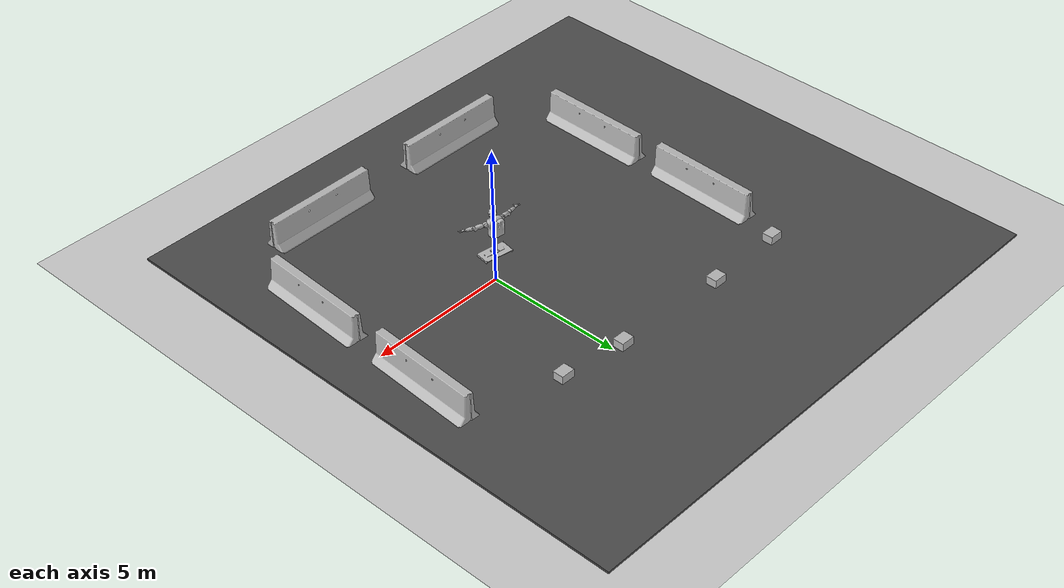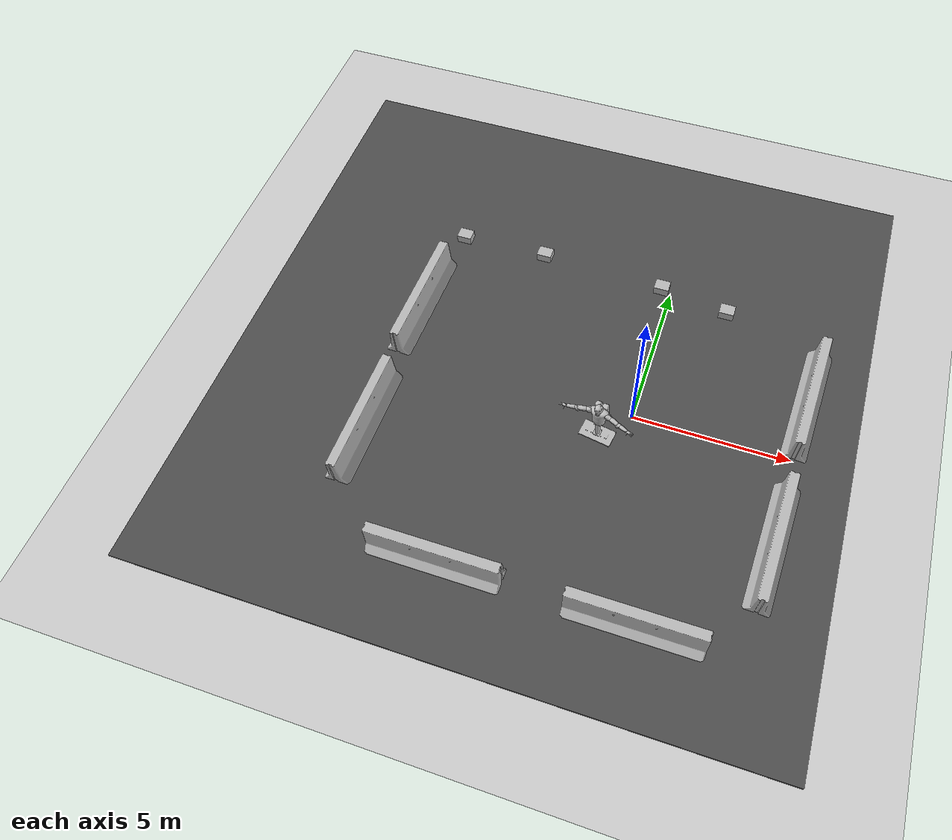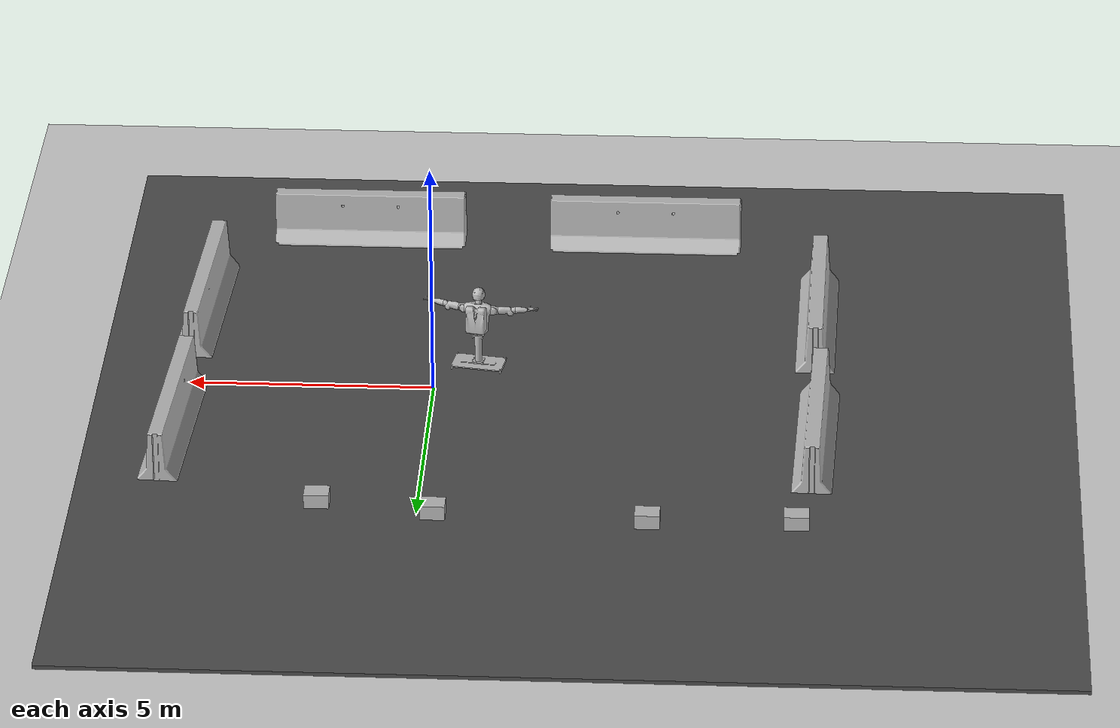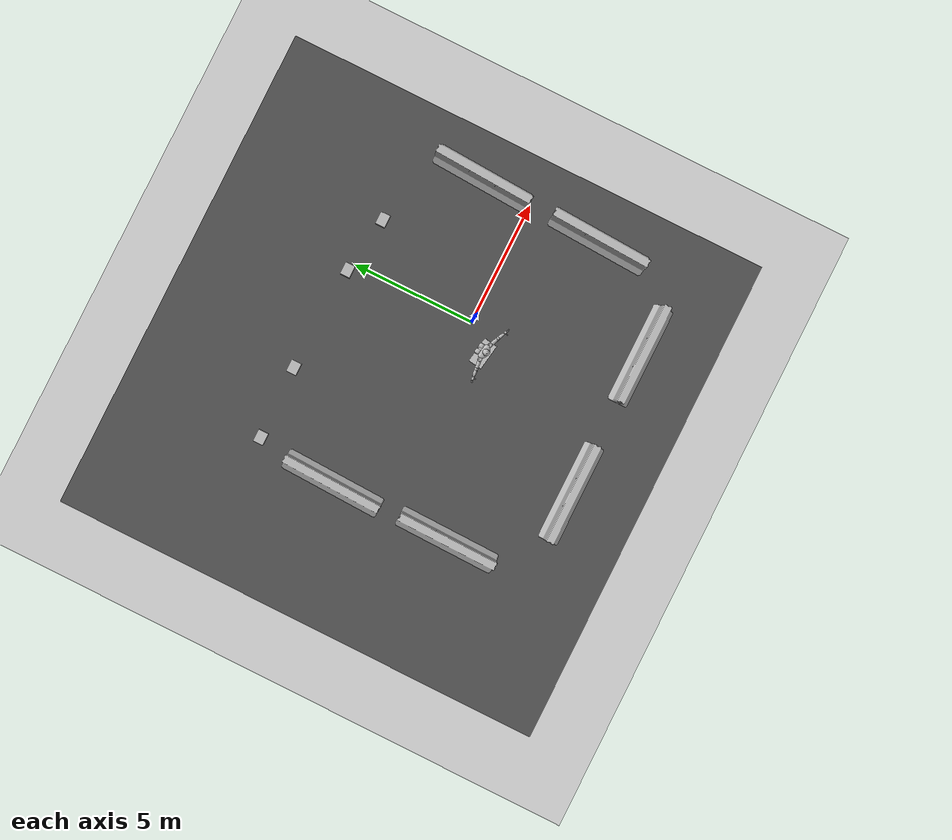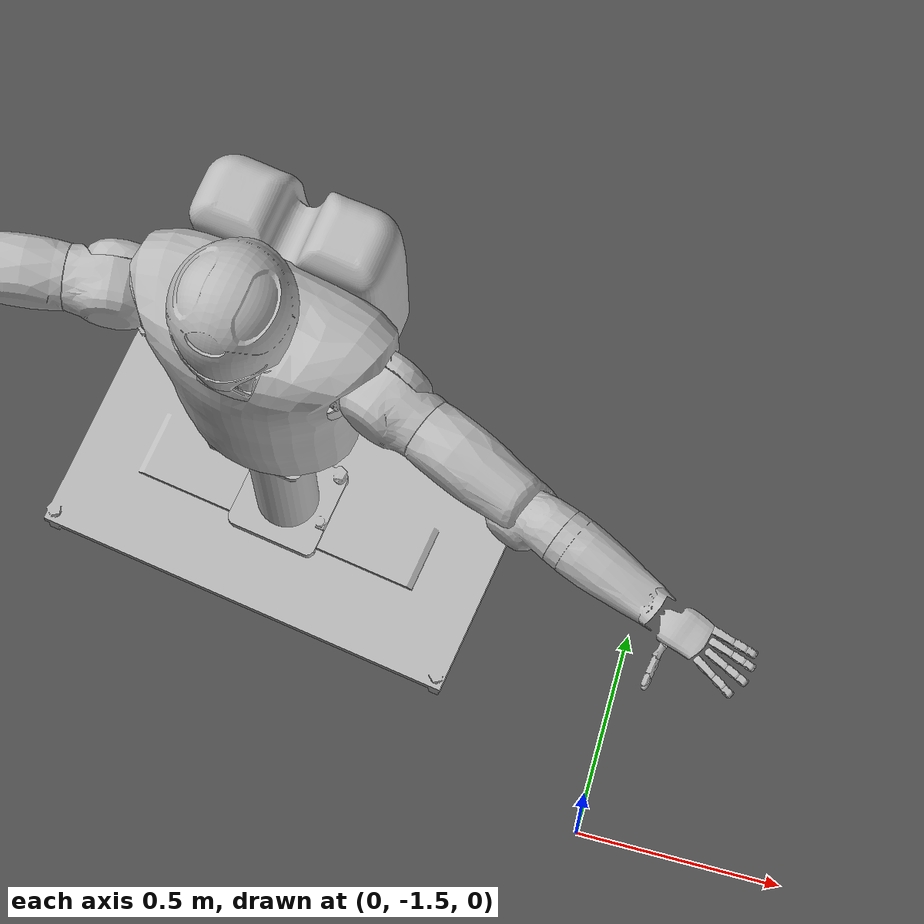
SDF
<sdf version="1.7">
 <world name="default">
  <light name="sun" type="directional">
   <pose>0 0 10 0 -0 0</pose>
   <diffuse>0.8 0.8 0.8 1</diffuse>
   <specular>0.2 0.2 0.2 1</specular>
   <attenuation>
    <range>1000</range>
    <constant>0.9</constant>
    <linear>0.01</linear>
    <quadratic>0.001</quadratic>
   </attenuation>
   <direction>-0.5 0.1 -0.9</direction>
   <spot><inner_angle>0</inner_angle><outer_angle>0</outer_angle><falloff>0</falloff></spot>
  </light>
  <model name="ground_plane">
   <static>1</static>
   <link name="link">
    <collision name="collision">
     <geometry><plane><normal>0 0 1</normal><size>100 100</size></plane></geometry>
     <surface>
      <contact><collide_bitmask>65535</collide_bitmask></contact>
      <friction><ode><mu>100</mu><mu2>50</mu2></ode></friction>
     </surface>
    </collision>
    <visual name="visual">
     <cast_shadows>0</cast_shadows>
     <geometry><plane><normal>0 0 1</normal><size>100 100</size></plane></geometry>
     <material>
      <script><uri>file://media/materials/scripts/gazebo.material</uri><name>Gazebo/Grey</name></script>
     </material>
    </visual>
   </link>
  </model>
  <gravity>0 0 -9.8</gravity>
  <magnetic_field>6e-06 2.3e-05 -4.2e-05</magnetic_field>
  <atmosphere type="adiabatic"/>
  <physics type="ode">
   <max_step_size>0.001</max_step_size>
   <real_time_factor>1</real_time_factor>
   <real_time_update_rate>1000</real_time_update_rate>
  </physics>
  <scene><ambient>0.4 0.4 0.4 1</ambient><background>0.7 0.7 0.7 1</background><shadows>1</shadows></scene>
  <spherical_coordinates>
   <surface_model>EARTH_WGS84</surface_model>
   <latitude_deg>0</latitude_deg>
   <longitude_deg>0</longitude_deg>
   <elevation>0</elevation>
   <heading_deg>0</heading_deg>
  </spherical_coordinates>
  <model name="asphalt_plane">
   <static>1</static>
   <link name="link">
    <collision name="collision"><geometry><box><size>20 20 0.1</size></box></geometry></collision>
    <visual name="visual">
     <cast_shadows>0</cast_shadows>
     <geometry><box><size>20 20 0.1</size></box></geometry>
     <material>
      <script>
       <uri>model://asphalt_plane/materials/scripts</uri>
       <uri>model://asphalt_plane/materials/textures</uri>
       <name>vrc/asphalt</name>
      </script>
     </material>
    </visual>
   </link>
   <pose>-3.13023 0.98883 0 0 -0 0</pose>
  </model>
  <model name="cardboard_box">
   <pose>-7.5154 5.21849 0.199 0 -0 0</pose>
   <link name="link">
    <inertial>
     <mass>2</mass>
     <inertia>
      <ixx>0.0416667</ixx>
      <ixy>0</ixy>
      <ixz>0</ixz>
      <iyy>0.0566667</iyy>
      <iyz>0</iyz>
      <izz>0.0683333</izz>
     </inertia>
    </inertial>
    <collision name="collision">
     <geometry><box><size>0.5 0.4 0.3</size></box></geometry>
     <surface>
      <friction><ode><mu>1</mu><mu2>1</mu2></ode></friction>
      <contact><ode><kp>1e+07</kp><kd>1</kd><min_depth>0.001</min_depth><max_vel>0.1</max_vel></ode></contact>
     </surface>
    </collision>
    <visual name="visual">
     <pose>0 0 -0.15 0 -0 0</pose>
     <geometry>
      <mesh><uri>model://cardboard_box/meshes/cardboard_box.dae</uri><scale>1.25932 1.00745 0.755591</scale></mesh>
     </geometry>
    </visual>
   </link>
  </model>
  <model name="cardboard_box_0">
   <pose>-4.57723 5.28688 0.199 0 -0 0</pose>
   <link name="link">
    <inertial>
     <mass>2</mass>
     <inertia>
      <ixx>0.0416667</ixx>
      <ixy>0</ixy>
      <ixz>0</ixz>
      <iyy>0.0566667</iyy>
      <iyz>0</iyz>
      <izz>0.0683333</izz>
     </inertia>
    </inertial>
    <collision name="collision">
     <geometry><box><size>0.5 0.4 0.3</size></box></geometry>
     <surface>
      <friction><ode><mu>1</mu><mu2>1</mu2></ode></friction>
      <contact><ode><kp>1e+07</kp><kd>1</kd><min_depth>0.001</min_depth><max_vel>0.1</max_vel></ode></contact>
     </surface>
    </collision>
    <visual name="visual">
     <pose>0 0 -0.15 0 -0 0</pose>
     <geometry>
      <mesh><uri>model://cardboard_box/meshes/cardboard_box.dae</uri><scale>1.25932 1.00745 0.755591</scale></mesh>
     </geometry>
    </visual>
   </link>
  </model>
  <model name="cardboard_box_1">
   <pose>1.98528 4.78466 0.199 0 -0 0</pose>
   <link name="link">
    <inertial>
     <mass>2</mass>
     <inertia>
      <ixx>0.0416667</ixx>
      <ixy>0</ixy>
      <ixz>0</ixz>
      <iyy>0.0566667</iyy>
      <iyz>0</iyz>
      <izz>0.0683333</izz>
     </inertia>
    </inertial>
    <collision name="collision">
     <geometry><box><size>0.5 0.4 0.3</size></box></geometry>
     <surface>
      <friction><ode><mu>1</mu><mu2>1</mu2></ode></friction>
      <contact><ode><kp>1e+07</kp><kd>1</kd><min_depth>0.001</min_depth><max_vel>0.1</max_vel></ode></contact>
     </surface>
    </collision>
    <visual name="visual">
     <pose>0 0 -0.15 0 -0 0</pose>
     <geometry>
      <mesh><uri>model://cardboard_box/meshes/cardboard_box.dae</uri><scale>1.25932 1.00745 0.755591</scale></mesh>
     </geometry>
    </visual>
   </link>
  </model>
  <model name="cardboard_box_2">
   <pose>-0.334783 5.12349 0.199 0 -0 0</pose>
   <link name="link">
    <inertial>
     <mass>2</mass>
     <inertia>
      <ixx>0.0416667</ixx>
      <ixy>0</ixy>
      <ixz>0</ixz>
      <iyy>0.0566667</iyy>
      <iyz>0</iyz>
      <izz>0.0683333</izz>
     </inertia>
    </inertial>
    <collision name="collision">
     <geometry><box><size>0.5 0.4 0.3</size></box></geometry>
     <surface>
      <friction><ode><mu>1</mu><mu2>1</mu2></ode></friction>
      <contact><ode><kp>1e+07</kp><kd>1</kd><min_depth>0.001</min_depth><max_vel>0.1</max_vel></ode></contact>
     </surface>
    </collision>
    <visual name="visual">
     <pose>0 0 -0.15 0 -0 0</pose>
     <geometry>
      <mesh><uri>model://cardboard_box/meshes/cardboard_box.dae</uri><scale>1.25932 1.00745 0.755591</scale></mesh>
     </geometry>
    </visual>
   </link>
  </model>
  <model name="jersey_barrier">
   <static>1</static>
   <link name="link">
    <visual name="visual">
     <geometry><mesh><uri>model://jersey_barrier/meshes/jersey_barrier.dae</uri></mesh></geometry>
    </visual>
    <collision name="upright">
     <pose>0 0 0.5715 0 -0 0</pose>
     <geometry><box><size>4.06542 0.3063 1.143</size></box></geometry>
    </collision>
    <collision name="base">
     <pose>0 0 0.032258 0 -0 0</pose>
     <geometry><box><size>4.06542 0.8107 0.064516</size></box></geometry>
    </collision>
    <collision name="base2">
     <pose>0 0 0.1 0 -0 0</pose>
     <geometry><box><size>4.06542 0.65 0.1</size></box></geometry>
    </collision>
    <collision name="base3">
     <pose>0 0 0.2 0 -0 0</pose>
     <geometry><box><size>4.06542 0.5 0.1</size></box></geometry>
    </collision>
    <collision name="left-angle">
     <pose>0 -0.224 0.2401 0.9 -0 0</pose>
     <geometry><box><size>4.06542 0.5 0.064516</size></box></geometry>
    </collision>
    <collision name="right-angle">
     <pose>0 0.224 0.2401 -0.9 0 0</pose>
     <geometry><box><size>4.06542 0.5 0.064516</size></box></geometry>
    </collision>
   </link>
   <pose>-4.13725 -6.29572 0 0 -0 0</pose>
  </model>
  <model name="jersey_barrier_0">
   <static>1</static>
   <link name="link">
    <visual name="visual">
     <geometry><mesh><uri>model://jersey_barrier/meshes/jersey_barrier.dae</uri></mesh></geometry>
    </visual>
    <collision name="upright">
     <pose>0 0 0.5715 0 -0 0</pose>
     <geometry><box><size>4.06542 0.3063 1.143</size></box></geometry>
    </collision>
    <collision name="base">
     <pose>0 0 0.032258 0 -0 0</pose>
     <geometry><box><size>4.06542 0.8107 0.064516</size></box></geometry>
    </collision>
    <collision name="base2">
     <pose>0 0 0.1 0 -0 0</pose>
     <geometry><box><size>4.06542 0.65 0.1</size></box></geometry>
    </collision>
    <collision name="base3">
     <pose>0 0 0.2 0 -0 0</pose>
     <geometry><box><size>4.06542 0.5 0.1</size></box></geometry>
    </collision>
    <collision name="left-angle">
     <pose>0 -0.224 0.2401 0.9 -0 0</pose>
     <geometry><box><size>4.06542 0.5 0.064516</size></box></geometry>
    </collision>
    <collision name="right-angle">
     <pose>0 0.224 0.2401 -0.9 0 0</pose>
     <geometry><box><size>4.06542 0.5 0.064516</size></box></geometry>
    </collision>
   </link>
   <pose>1.74869 -6.33802 0 0 -0 0</pose>
  </model>
  <model name="jersey_barrier_1">
   <static>1</static>
   <link name="link">
    <visual name="visual">
     <geometry><mesh><uri>model://jersey_barrier/meshes/jersey_barrier.dae</uri></mesh></geometry>
    </visual>
    <collision name="upright">
     <pose>0 0 0.5715 0 -0 0</pose>
     <geometry><box><size>4.06542 0.3063 1.143</size></box></geometry>
    </collision>
    <collision name="base">
     <pose>0 0 0.032258 0 -0 0</pose>
     <geometry><box><size>4.06542 0.8107 0.064516</size></box></geometry>
    </collision>
    <collision name="base2">
     <pose>0 0 0.1 0 -0 0</pose>
     <geometry><box><size>4.06542 0.65 0.1</size></box></geometry>
    </collision>
    <collision name="base3">
     <pose>0 0 0.2 0 -0 0</pose>
     <geometry><box><size>4.06542 0.5 0.1</size></box></geometry>
    </collision>
    <collision name="left-angle">
     <pose>0 -0.224 0.2401 0.9 -0 0</pose>
     <geometry><box><size>4.06542 0.5 0.064516</size></box></geometry>
    </collision>
    <collision name="right-angle">
     <pose>0 0.224 0.2401 -0.9 0 0</pose>
     <geometry><box><size>4.06542 0.5 0.064516</size></box></geometry>
    </collision>
   </link>
   <pose>-7.8424 -2.85387 0 0 -0 1.55378</pose>
  </model>
  <model name="jersey_barrier_2">
   <static>1</static>
   <link name="link">
    <visual name="visual">
     <geometry><mesh><uri>model://jersey_barrier/meshes/jersey_barrier.dae</uri></mesh></geometry>
    </visual>
    <collision name="upright">
     <pose>0 0 0.5715 0 -0 0</pose>
     <geometry><box><size>4.06542 0.3063 1.143</size></box></geometry>
    </collision>
    <collision name="base">
     <pose>0 0 0.032258 0 -0 0</pose>
     <geometry><box><size>4.06542 0.8107 0.064516</size></box></geometry>
    </collision>
    <collision name="base2">
     <pose>0 0 0.1 0 -0 0</pose>
     <geometry><box><size>4.06542 0.65 0.1</size></box></geometry>
    </collision>
    <collision name="base3">
     <pose>0 0 0.2 0 -0 0</pose>
     <geometry><box><size>4.06542 0.5 0.1</size></box></geometry>
    </collision>
    <collision name="left-angle">
     <pose>0 -0.224 0.2401 0.9 -0 0</pose>
     <geometry><box><size>4.06542 0.5 0.064516</size></box></geometry>
    </collision>
    <collision name="right-angle">
     <pose>0 0.224 0.2401 -0.9 0 0</pose>
     <geometry><box><size>4.06542 0.5 0.064516</size></box></geometry>
    </collision>
   </link>
   <pose>4.95637 -2.95521 0 0 -0 1.52217</pose>
  </model>
  <model name="jersey_barrier_3">
   <static>1</static>
   <link name="link">
    <visual name="visual">
     <geometry><mesh><uri>model://jersey_barrier/meshes/jersey_barrier.dae</uri></mesh></geometry>
    </visual>
    <collision name="upright">
     <pose>0 0 0.5715 0 -0 0</pose>
     <geometry><box><size>4.06542 0.3063 1.143</size></box></geometry>
    </collision>
    <collision name="base">
     <pose>0 0 0.032258 0 -0 0</pose>
     <geometry><box><size>4.06542 0.8107 0.064516</size></box></geometry>
    </collision>
    <collision name="base2">
     <pose>0 0 0.1 0 -0 0</pose>
     <geometry><box><size>4.06542 0.65 0.1</size></box></geometry>
    </collision>
    <collision name="base3">
     <pose>0 0 0.2 0 -0 0</pose>
     <geometry><box><size>4.06542 0.5 0.1</size></box></geometry>
    </collision>
    <collision name="left-angle">
     <pose>0 -0.224 0.2401 0.9 -0 0</pose>
     <geometry><box><size>4.06542 0.5 0.064516</size></box></geometry>
    </collision>
    <collision name="right-angle">
     <pose>0 0.224 0.2401 -0.9 0 0</pose>
     <geometry><box><size>4.06542 0.5 0.064516</size></box></geometry>
    </collision>
   </link>
   <pose>5.13964 2.07137 0 0 -0 1.51773</pose>
  </model>
  <model name="jersey_barrier_4">
   <static>1</static>
   <link name="link">
    <visual name="visual">
     <geometry><mesh><uri>model://jersey_barrier/meshes/jersey_barrier.dae</uri></mesh></geometry>
    </visual>
    <collision name="upright">
     <pose>0 0 0.5715 0 -0 0</pose>
     <geometry><box><size>4.06542 0.3063 1.143</size></box></geometry>
    </collision>
    <collision name="base">
     <pose>0 0 0.032258 0 -0 0</pose>
     <geometry><box><size>4.06542 0.8107 0.064516</size></box></geometry>
    </collision>
    <collision name="base2">
     <pose>0 0 0.1 0 -0 0</pose>
     <geometry><box><size>4.06542 0.65 0.1</size></box></geometry>
    </collision>
    <collision name="base3">
     <pose>0 0 0.2 0 -0 0</pose>
     <geometry><box><size>4.06542 0.5 0.1</size></box></geometry>
    </collision>
    <collision name="left-angle">
     <pose>0 -0.224 0.2401 0.9 -0 0</pose>
     <geometry><box><size>4.06542 0.5 0.064516</size></box></geometry>
    </collision>
    <collision name="right-angle">
     <pose>0 0.224 0.2401 -0.9 0 0</pose>
     <geometry><box><size>4.06542 0.5 0.064516</size></box></geometry>
    </collision>
   </link>
   <pose>-7.86009 1.99781 0 0 -0 1.53779</pose>
  </model>
  <model name="r2">
   <link name="/r2/robot_world">
    <inertial>
     <pose>0 0 0.625017 0 -0 0</pose>
     <mass>56.01</mass>
     <inertia>
      <ixx>14.6261</ixx>
      <ixy>-3.58342e-06</ixy>
      <ixz>-5.7072e-09</ixz>
      <iyy>14.6252</iyy>
      <iyz>-1.43337e-06</iyz>
      <izz>12.001</izz>
     </inertia>
    </inertial>
    <collision name="/r2/robot_world_collision_/r2/baseplate">
     <pose>0 0 0 1.57 0 3.14</pose>
     <geometry>
      <mesh><scale>1 1 1</scale><uri>model://robonaut/meshes/Stanchion_Baseplate.dae</uri></mesh>
     </geometry>
    </collision>
    <collision name="/r2/robot_world_collision_/r2/stanchion">
     <pose>0 0 0.4 0 -0 -1.57319</pose>
     <geometry><cylinder><length>0.5</length><radius>0.075</radius></cylinder></geometry>
    </collision>
    <visual name="/r2/robot_world_visual_/r2/baseplate">
     <pose>0 0 0 1.57 0 3.14</pose>
     <geometry>
      <mesh><scale>1 1 1</scale><uri>model://robonaut/meshes/Stanchion_Baseplate.dae</uri></mesh>
     </geometry>
    </visual>
    <visual name="/r2/robot_world_visual_/r2/stanchion">
     <pose>0 0 0.7 0 -0 -1.57319</pose>
     <geometry><mesh><scale>1 1 1</scale><uri>model://robonaut/meshes/Stanchion.dae</uri></mesh></geometry>
    </visual>
    <velocity_decay><linear>0</linear><angular>0</angular></velocity_decay>
   </link>
   <link name="/r2/waist_center">
    <pose>0 0 0.72 -3.14159 0.001593 -1.57478</pose>
    <inertial>
     <pose>2.3e-05 0 -0.00027 0 -0 0</pose>
     <mass>20.13</mass>
     <inertia>
      <ixx>2.00426</ixx>
      <ixy>0</ixy>
      <ixz>-0.000355745</ixz>
      <iyy>2.00716</iyy>
      <iyz>0</iyz>
      <izz>2.0042</izz>
     </inertia>
    </inertial>
    <collision name="/r2/waist_center_collision">
     <pose>0.02 0.05 -0.5625 -1.57 -0 -1.57</pose>
     <geometry><mesh><scale>1 1 1</scale><uri>model://robonaut/meshes/Body.dae</uri></mesh></geometry>
    </collision>
    <collision name="/r2/waist_center_collision_/r2/backpack">
     <pose>0 0 -0.54 0 -0 0.25</pose>
     <geometry><mesh><scale>1 1 1</scale><uri>model://robonaut/meshes/Backpack.dae</uri></mesh></geometry>
    </collision>
    <collision name="/r2/waist_center_collision_/r2/body_cover">
     <pose>0.02 0.05 -0.5625 -1.57 -0 -1.57</pose>
     <geometry><mesh><scale>1 1 1</scale><uri>model://robonaut/meshes/Body_Cover.dae</uri></mesh></geometry>
    </collision>
    <visual name="/r2/waist_center_visual">
     <pose>0.02 0.05 -0.5625 -1.57 -0 -1.57</pose>
     <geometry><mesh><scale>1 1 1</scale><uri>model://robonaut/meshes/Body.dae</uri></mesh></geometry>
    </visual>
    <visual name="/r2/waist_center_visual_/r2/backpack">
     <pose>0 0 -0.54 0 -0 0.25</pose>
     <geometry><mesh><scale>1 1 1</scale><uri>model://robonaut/meshes/Backpack.dae</uri></mesh></geometry>
    </visual>
    <visual name="/r2/waist_center_visual_/r2/body_cover">
     <pose>0.02 0.05 -0.5625 -1.57 -0 -1.57</pose>
     <geometry><mesh><scale>1 1 1</scale><uri>model://robonaut/meshes/Body_Cover.dae</uri></mesh></geometry>
    </visual>
    <velocity_decay><linear>0</linear><angular>0</angular></velocity_decay>
   </link>
   <joint name="/r2/waist/joint0" type="revolute">
    <child>/r2/waist_center</child>
    <parent>/r2/robot_world</parent>
    <axis>
     <xyz expressed_in="__model__">6e-06 0.001593 -0.999999</xyz>
     <limit><lower>-3.14</lower><upper>3.14</upper><effort>1e+07</effort><velocity>1000</velocity></limit>
     <dynamics>
      <damping>10</damping>
      <spring_reference>0</spring_reference>
      <spring_stiffness>0</spring_stiffness>
     </dynamics>
    </axis>
    <physics><ode><limit><cfm>0</cfm><erp>0.2</erp></limit></ode></physics>
   </joint>
   <link name="/r2/left_shoulder_roll">
    <pose>0.000257 0.064475 1.26435 1.5756 -0.001539 1.30542</pose>
    <inertial>
     <pose>-0.008992 -0.001316 0.10287 0 -0 0</pose>
     <mass>6.16886</mass>
     <inertia>
      <ixx>0.0198585</ixx>
      <ixy>-0.0060196</ixy>
      <ixz>-0.000395063</ixz>
      <iyy>0.0671901</iyy>
      <iyz>0.00012683</iyz>
      <izz>0.063415</izz>
     </inertia>
    </inertial>
    <collision name="/r2/left_shoulder_roll_collision">
     <pose>0 0 0.08 0 -0 1.57</pose>
     <geometry>
      <mesh><scale>1 1 1</scale><uri>model://robonaut/meshes/Left_Shoulder_Upper.dae</uri></mesh>
     </geometry>
    </collision>
    <visual name="/r2/left_shoulder_roll_visual">
     <pose>0 0 0.08 0 -0 1.57</pose>
     <geometry>
      <mesh><scale>1 1 1</scale><uri>model://robonaut/meshes/Left_Shoulder_Upper.dae</uri></mesh>
     </geometry>
    </visual>
    <velocity_decay><linear>0</linear><angular>0</angular></velocity_decay>
   </link>
   <joint name="/r2/left_arm/joint0" type="revolute">
    <child>/r2/left_shoulder_roll</child>
    <parent>/r2/waist_center</parent>
    <axis>
     <xyz expressed_in="__model__">0.964985 -0.262261 -0.004808</xyz>
     <limit><lower>-1.57</lower><upper>1.57</upper><effort>100</effort><velocity>1000</velocity></limit>
     <dynamics>
      <damping>10</damping>
      <spring_reference>0</spring_reference>
      <spring_stiffness>0</spring_stiffness>
     </dynamics>
    </axis>
    <physics><ode><limit><cfm>0</cfm><erp>0.2</erp></limit></ode></physics>
   </joint>
   <link name="/r2/left_shoulder_pitch">
    <pose>0.305782 -0.01856 1.26283 1.88114 -1.56575 -0.575018</pose>
    <inertial>
     <pose>0.037084 -0.000284 0.007798 0 -0 0</pose>
     <mass>4.42706</mass>
     <inertia>
      <ixx>0.0270106</ixx>
      <ixy>0.00151295</ixy>
      <ixz>-5.23825e-05</ixz>
      <iyy>0.0113837</iyy>
      <iyz>2.17139e-05</iyz>
      <izz>0.0251963</izz>
     </inertia>
    </inertial>
    <collision name="/r2/left_shoulder_pitch_collision">
     <pose>0 0 0 0 0 -1.57</pose>
     <geometry>
      <mesh><scale>1 1 1</scale><uri>model://robonaut/meshes/Left_Shoulder_Lower.dae</uri></mesh>
     </geometry>
    </collision>
    <visual name="/r2/left_shoulder_pitch_visual">
     <pose>0 0 0 0 0 -1.57</pose>
     <geometry>
      <mesh><scale>1 1 1</scale><uri>model://robonaut/meshes/Left_Shoulder_Lower.dae</uri></mesh>
     </geometry>
    </visual>
    <velocity_decay><linear>0</linear><angular>0</angular></velocity_decay>
   </link>
   <joint name="/r2/left_arm/joint1" type="revolute">
    <child>/r2/left_shoulder_pitch</child>
    <parent>/r2/left_shoulder_roll</parent>
    <axis>
     <xyz expressed_in="__model__">-0.261598 -0.965176 -0.001542</xyz>
     <limit><lower>-1.66</lower><upper>0.175</upper><effort>100</effort><velocity>1000</velocity></limit>
     <dynamics>
      <damping>10</damping>
      <spring_reference>0</spring_reference>
      <spring_stiffness>0</spring_stiffness>
     </dynamics>
    </axis>
    <physics><ode><limit><cfm>0</cfm><erp>0.2</erp></limit></ode></physics>
   </joint>
   <link name="/r2/left_upper_arm">
    <pose>0.305782 -0.01856 1.26283 -2.83205 -1.56575 -0.575018</pose>
    <inertial>
     <pose>-0.007417 -0.041402 0.1016 0 -0 0</pose>
     <mass>4.85344</mass>
     <inertia>
      <ixx>0.0160074</ixx>
      <ixy>-0.00339462</ixy>
      <ixz>0.00658439</ixz>
      <iyy>0.0462371</iyy>
      <iyz>0.00137541</iyz>
      <izz>0.0421401</izz>
     </inertia>
    </inertial>
    <collision name="/r2/left_upper_arm_collision">
     <pose>0 0 0.1016 0 -0 3.14</pose>
     <geometry><mesh><scale>1 1 1</scale><uri>model://robonaut/meshes/Left_Upper_Arm.dae</uri></mesh></geometry>
    </collision>
    <visual name="/r2/left_upper_arm_visual">
     <pose>0 0 0.1016 0 -0 3.14</pose>
     <geometry><mesh><scale>1 1 1</scale><uri>model://robonaut/meshes/Left_Upper_Arm.dae</uri></mesh></geometry>
    </visual>
    <velocity_decay><linear>0</linear><angular>0</angular></velocity_decay>
   </link>
   <joint name="/r2/left_arm/joint2" type="revolute">
    <child>/r2/left_upper_arm</child>
    <parent>/r2/left_shoulder_pitch</parent>
    <axis>
     <xyz expressed_in="__model__">0.964959 -0.262357 -0.004808</xyz>
     <limit><lower>-4.89</lower><upper>-0.79</upper><effort>100</effort><velocity>1000</velocity></limit>
     <dynamics>
      <damping>10</damping>
      <spring_reference>0</spring_reference>
      <spring_stiffness>0</spring_stiffness>
     </dynamics>
    </axis>
    <physics><ode><limit><cfm>0</cfm><erp>0.2</erp></limit></ode></physics>
   </joint>
   <link name="/r2/left_elbow">
    <pose>0.649499 -0.111925 1.20674 1.87634 -1.56575 -0.575018</pose>
    <inertial>
     <pose>0.026162 0.033782 0.015443 0 -0 0</pose>
     <mass>2.97103</mass>
     <inertia>
      <ixx>0.0120275</ixx>
      <ixy>0.00164171</ixy>
      <ixz>-0.00118812</ixz>
      <iyy>0.00883772</iyy>
      <iyz>0.00316051</iyz>
      <izz>0.010535</izz>
     </inertia>
    </inertial>
    <collision name="/r2/left_elbow_collision">
     <pose>0 0 0 0 0 -1.57</pose>
     <geometry><mesh><scale>1 1 1</scale><uri>model://robonaut/meshes/Left_Elbow.dae</uri></mesh></geometry>
    </collision>
    <visual name="/r2/left_elbow_visual">
     <pose>0 0 0 0 0 -1.57</pose>
     <geometry><mesh><scale>1 1 1</scale><uri>model://robonaut/meshes/Left_Elbow.dae</uri></mesh></geometry>
    </visual>
    <velocity_decay><linear>0</linear><angular>0</angular></velocity_decay>
   </link>
   <joint name="/r2/left_arm/joint3" type="revolute">
    <child>/r2/left_elbow</child>
    <parent>/r2/left_upper_arm</parent>
    <axis>
     <xyz expressed_in="__model__">-0.266228 -0.963909 -0.001518</xyz>
     <limit><lower>-2.79</lower><upper>-0.087</upper><effort>100</effort><velocity>1000</velocity></limit>
     <dynamics>
      <damping>1</damping>
      <spring_reference>0</spring_reference>
      <spring_stiffness>0</spring_stiffness>
     </dynamics>
    </axis>
    <physics><ode><limit><cfm>0</cfm><erp>0.2</erp></limit></ode></physics>
   </joint>
   <link name="/r2/left_lower_arm">
    <pose>0.649728 -0.112073 1.26077 -2.83305 -1.56575 -0.575018</pose>
    <inertial>
     <pose>0.000356 -0.001227 0.17653 0 -0 0</pose>
     <mass>6.93996</mass>
     <inertia>
      <ixx>0.012525</ixx>
      <ixy>-0.000244647</ixy>
      <ixz>0.000520899</ixz>
      <iyy>0.0395064</iyy>
      <iyz>-0.000169146</iyz>
      <izz>0.0403843</izz>
     </inertia>
    </inertial>
    <collision name="/r2/left_lower_arm_collision">
     <pose>0 0 0.1 0 -0 0</pose>
     <geometry><mesh><scale>1 1 1</scale><uri>model://robonaut/meshes/Left_Forearm.dae</uri></mesh></geometry>
    </collision>
    <visual name="/r2/left_lower_arm_visual">
     <pose>0 0 0.1 0 -0 0</pose>
     <geometry><mesh><scale>1 1 1</scale><uri>model://robonaut/meshes/Left_Forearm.dae</uri></mesh></geometry>
    </visual>
    <velocity_decay><linear>0</linear><angular>0</angular></velocity_decay>
   </link>
   <joint name="/r2/left_arm/joint4" type="revolute">
    <child>/r2/left_lower_arm</child>
    <parent>/r2/left_elbow</parent>
    <axis>
     <xyz expressed_in="__model__">0.964696 -0.263322 -0.00481</xyz>
     <limit><lower>-1.3</lower><upper>4.45</upper><effort>100</effort><velocity>1000</velocity></limit>
     <dynamics>
      <damping>1</damping>
      <spring_reference>0</spring_reference>
      <spring_stiffness>0</spring_stiffness>
     </dynamics>
    </axis>
    <physics><ode><limit><cfm>0</cfm><erp>0.2</erp></limit></ode></physics>
   </joint>
   <link name="/r2/left_wrist_pitch">
    <pose>0.994171 -0.206092 1.25906 1.85494 -1.56575 -0.575018</pose>
    <inertial>
     <pose>-0.004064 0 -0.000922 0 -0 0</pose>
     <mass>0.116573</mass>
     <inertia>
      <ixx>5.765e-05</ixx>
      <ixy>4.36e-11</ixy>
      <ixz>1.75876e-06</ixz>
      <iyy>1.69438e-05</iyy>
      <iyz>5.4431e-08</iyz>
      <izz>4.41886e-05</izz>
     </inertia>
    </inertial>
    <velocity_decay><linear>0</linear><angular>0</angular></velocity_decay>
   </link>
   <joint name="/r2/left_arm/joint5" type="revolute">
    <child>/r2/left_wrist_pitch</child>
    <parent>/r2/left_lower_arm</parent>
    <axis>
     <xyz expressed_in="__model__">-0.286793 -0.957991 -0.001415</xyz>
     <limit><lower>-1.22</lower><upper>1.22</upper><effort>100</effort><velocity>1000</velocity></limit>
     <dynamics>
      <damping>1</damping>
      <spring_reference>0</spring_reference>
      <spring_stiffness>0</spring_stiffness>
     </dynamics>
    </axis>
    <physics><ode><limit><cfm>0</cfm><erp>0.2</erp></limit></ode></physics>
   </joint>
   <link name="/r2/left_wrist_yaw">
    <pose>0.999988 -0.207833 1.25901 -3.06047 0.006749 -0.290868</pose>
    <inertial>
     <pose>0.033205 -0.025812 0.033286 0 -0 0</pose>
     <mass>2.37882</mass>
     <inertia>
      <ixx>0.0112391</ixx>
      <ixy>0.000520047</ixy>
      <ixz>0.00298821</ixz>
      <iyy>0.0135826</iyy>
      <iyz>0.000437366</iyz>
      <izz>0.0112115</izz>
     </inertia>
    </inertial>
    <collision name="/r2/left_wrist_yaw_collision_/r2/left_palm">
     <pose>0 0 0 3.14 -0 1.556</pose>
     <geometry><mesh><scale>1 1 1</scale><uri>model://robonaut/meshes/Left_Palm.dae</uri></mesh></geometry>
    </collision>
    <visual name="/r2/left_wrist_yaw_visual_/r2/left_palm">
     <pose>0 0 0 3.14 -0 1.556</pose>
     <geometry><mesh><scale>1 1 1</scale><uri>model://robonaut/meshes/Left_Palm.dae</uri></mesh></geometry>
    </visual>
    <velocity_decay><linear>0</linear><angular>0</angular></velocity_decay>
    <velocity_decay><linear>0</linear><angular>0</angular></velocity_decay>
    <velocity_decay><linear>0</linear><angular>0</angular></velocity_decay>
    <velocity_decay><linear>0</linear><angular>0</angular></velocity_decay>
   </link>
   <joint name="/r2/left_arm/joint6" type="revolute">
    <child>/r2/left_wrist_yaw</child>
    <parent>/r2/left_wrist_pitch</parent>
    <axis>
     <xyz expressed_in="__model__">0.016794 0.079555 -0.996689</xyz>
     <limit><lower>-0.785</lower><upper>0.785</upper><effort>100</effort><velocity>1000</velocity></limit>
     <dynamics>
      <damping>1</damping>
      <spring_reference>0</spring_reference>
      <spring_stiffness>0</spring_stiffness>
     </dynamics>
    </axis>
    <physics><ode><limit><cfm>0</cfm><erp>0.2</erp></limit></ode></physics>
   </joint>
   <link name="/r2/left_index_yaw">
    <pose>1.08724 -0.263526 1.27225 -3.0619 0.016574 -0.412654</pose>
    <inertial>
     <mass>0.001</mass>
     <inertia><ixx>0.001</ixx><ixy>0</ixy><ixz>0</ixz><iyy>0.001</iyy><iyz>0</iyz><izz>0.001</izz></inertia>
    </inertial>
    <velocity_decay><linear>0</linear><angular>0</angular></velocity_decay>
   </link>
   <joint name="/r2/left_arm/hand/index/joint0" type="revolute">
    <child>/r2/left_index_yaw</child>
    <parent>/r2/left_wrist_yaw</parent>
    <axis>
     <xyz expressed_in="__model__">0.016794 0.079555 -0.996689</xyz>
     <limit><lower>-0.3491</lower><upper>0.3491</upper><effort>1e+07</effort><velocity>1000</velocity></limit>
     <dynamics>
      <damping>0.1</damping>
      <spring_reference>0</spring_reference>
      <spring_stiffness>0</spring_stiffness>
     </dynamics>
    </axis>
   </joint>
   <link name="/r2/left_index_proximal">
    <pose>1.09608 -0.267396 1.27209 -1.4911 0.016574 -0.412654</pose>
    <inertial>
     <mass>0.001</mass>
     <inertia><ixx>0.001</ixx><ixy>0</ixy><ixz>0</ixz><iyy>0.001</iyy><iyz>0</iyz><izz>0.001</izz></inertia>
    </inertial>
    <collision name="/r2/left_index_proximal_collision">
     <pose>0 0 0 0 -0 1.57</pose>
     <geometry><mesh><scale>1 1 1</scale><uri>model://robonaut/meshes/Finger_Proximal.dae</uri></mesh></geometry>
    </collision>
    <visual name="/r2/left_index_proximal_visual">
     <pose>0 0 0 0 -0 1.57</pose>
     <geometry><mesh><scale>1 1 1</scale><uri>model://robonaut/meshes/Finger_Proximal.dae</uri></mesh></geometry>
    </visual>
    <velocity_decay><linear>0</linear><angular>0</angular></velocity_decay>
   </link>
   <joint name="/r2/left_arm/hand/index/joint1" type="revolute">
    <child>/r2/left_index_proximal</child>
    <parent>/r2/left_index_yaw</parent>
    <axis>
     <xyz expressed_in="__model__">0.400978 0.912623 0.079601</xyz>
     <limit><lower>0</lower><upper>1.57</upper><effort>1e+07</effort><velocity>1000</velocity></limit>
     <dynamics>
      <damping>0.1</damping>
      <spring_reference>0</spring_reference>
      <spring_stiffness>0</spring_stiffness>
     </dynamics>
    </axis>
   </joint>
   <link name="/r2/left_index_medial">
    <pose>1.13679 -0.28522 1.27135 -1.4911 0.016574 -0.412654</pose>
    <inertial>
     <mass>0.001</mass>
     <inertia><ixx>0.001</ixx><ixy>0</ixy><ixz>0</ixz><iyy>0.001</iyy><iyz>0</iyz><izz>0.001</izz></inertia>
    </inertial>
    <collision name="/r2/left_index_medial_collision">
     <pose>0 0 0 3.14 0 1.57</pose>
     <geometry><mesh><scale>1 1 1</scale><uri>model://robonaut/meshes/Finger_Mid.dae</uri></mesh></geometry>
    </collision>
    <visual name="/r2/left_index_medial_visual">
     <pose>0 0 0 3.14 0 1.57</pose>
     <geometry><mesh><scale>1 1 1</scale><uri>model://robonaut/meshes/Finger_Mid.dae</uri></mesh></geometry>
    </visual>
    <velocity_decay><linear>0</linear><angular>0</angular></velocity_decay>
   </link>
   <joint name="/r2/left_arm/hand/index/joint2" type="revolute">
    <child>/r2/left_index_medial</child>
    <parent>/r2/left_index_proximal</parent>
    <axis>
     <xyz expressed_in="__model__">0.400978 0.912623 0.079601</xyz>
     <limit><lower>0</lower><upper>1.57</upper><effort>1e+07</effort><velocity>1000</velocity></limit>
     <dynamics>
      <damping>0.1</damping>
      <spring_reference>0</spring_reference>
      <spring_stiffness>0</spring_stiffness>
     </dynamics>
    </axis>
   </joint>
   <link name="/r2/left_index_distal">
    <pose>1.16471 -0.297442 1.27085 -1.4911 0.016574 -0.412654</pose>
    <inertial>
     <pose>0.012319 0 0 0 -0 0</pose>
     <mass>0.002</mass>
     <inertia>
      <ixx>0.002</ixx>
      <ixy>0</ixy>
      <ixz>0</ixz>
      <iyy>0.0020003</iyy>
      <iyz>0</iyz>
      <izz>0.0020003</izz>
     </inertia>
    </inertial>
    <collision name="/r2/left_index_distal_collision">
     <pose>0 0 0 0 -1.57 0</pose>
     <geometry><mesh><scale>1 1 1</scale><uri>model://robonaut/meshes/Finger_Dist.dae</uri></mesh></geometry>
    </collision>
    <visual name="/r2/left_index_distal_visual">
     <pose>0 0 0 0 -1.57 0</pose>
     <geometry><mesh><scale>1 1 1</scale><uri>model://robonaut/meshes/Finger_Dist.dae</uri></mesh></geometry>
    </visual>
    <velocity_decay><linear>0</linear><angular>0</angular></velocity_decay>
   </link>
   <joint name="/r2/left_arm/hand/index/joint3" type="revolute">
    <child>/r2/left_index_distal</child>
    <parent>/r2/left_index_medial</parent>
    <axis>
     <xyz expressed_in="__model__">0.400978 0.912623 0.079601</xyz>
     <limit><lower>0</lower><upper>1.57</upper><effort>1e+07</effort><velocity>1000</velocity></limit>
     <dynamics>
      <damping>0.1</damping>
      <spring_reference>0</spring_reference>
      <spring_stiffness>0</spring_stiffness>
     </dynamics>
    </axis>
   </joint>
   <link name="/r2/left_middle_yaw">
    <pose>1.10098 -0.242075 1.27419 -3.06047 0.006749 -0.290868</pose>
    <inertial>
     <mass>0.001</mass>
     <inertia><ixx>0.001</ixx><ixy>0</ixy><ixz>0</ixz><iyy>0.001</iyy><iyz>0</iyz><izz>0.001</izz></inertia>
    </inertial>
    <velocity_decay><linear>0</linear><angular>0</angular></velocity_decay>
   </link>
   <joint name="/r2/left_arm/hand/middle/joint0" type="revolute">
    <child>/r2/left_middle_yaw</child>
    <parent>/r2/left_wrist_yaw</parent>
    <axis>
     <xyz expressed_in="__model__">0.016794 0.079555 -0.996689</xyz>
     <limit><lower>-0.3491</lower><upper>0.3491</upper><effort>1e+07</effort><velocity>1000</velocity></limit>
     <dynamics>
      <damping>0.1</damping>
      <spring_reference>0</spring_reference>
      <spring_stiffness>0</spring_stiffness>
     </dynamics>
    </axis>
   </joint>
   <link name="/r2/left_middle_proximal">
    <pose>1.11023 -0.244843 1.27413 -1.48968 0.006749 -0.290868</pose>
    <inertial>
     <mass>0.001</mass>
     <inertia><ixx>0.001</ixx><ixy>0</ixy><ixz>0</ixz><iyy>0.001</iyy><iyz>0</iyz><izz>0.001</izz></inertia>
    </inertial>
    <collision name="/r2/left_middle_proximal_collision">
     <pose>0 0 0 0 -0 1.57</pose>
     <geometry><mesh><scale>1 1 1</scale><uri>model://robonaut/meshes/Finger_Proximal.dae</uri></mesh></geometry>
    </collision>
    <visual name="/r2/left_middle_proximal_visual">
     <pose>0 0 0 0 -0 1.57</pose>
     <geometry><mesh><scale>1 1 1</scale><uri>model://robonaut/meshes/Finger_Proximal.dae</uri></mesh></geometry>
    </visual>
    <velocity_decay><linear>0</linear><angular>0</angular></velocity_decay>
   </link>
   <joint name="/r2/left_arm/hand/middle/joint1" type="revolute">
    <child>/r2/left_middle_proximal</child>
    <parent>/r2/left_middle_yaw</parent>
    <axis>
     <xyz expressed_in="__model__">0.286365 0.954688 0.081028</xyz>
     <limit><lower>0</lower><upper>1.57</upper><effort>1e+07</effort><velocity>1000</velocity></limit>
     <dynamics>
      <damping>0.1</damping>
      <spring_reference>0</spring_reference>
      <spring_stiffness>0</spring_stiffness>
     </dynamics>
    </axis>
   </joint>
   <link name="/r2/left_middle_medial">
    <pose>1.15281 -0.25759 1.27383 -1.48968 0.006749 -0.290868</pose>
    <inertial>
     <mass>0.001</mass>
     <inertia><ixx>0.001</ixx><ixy>0</ixy><ixz>0</ixz><iyy>0.001</iyy><iyz>0</iyz><izz>0.001</izz></inertia>
    </inertial>
    <collision name="/r2/left_middle_medial_collision">
     <pose>0 0 0 3.14 0 1.57</pose>
     <geometry><mesh><scale>1 1 1</scale><uri>model://robonaut/meshes/Finger_Mid.dae</uri></mesh></geometry>
    </collision>
    <visual name="/r2/left_middle_medial_visual">
     <pose>0 0 0 3.14 0 1.57</pose>
     <geometry><mesh><scale>1 1 1</scale><uri>model://robonaut/meshes/Finger_Mid.dae</uri></mesh></geometry>
    </visual>
    <velocity_decay><linear>0</linear><angular>0</angular></velocity_decay>
   </link>
   <joint name="/r2/left_arm/hand/middle/joint2" type="revolute">
    <child>/r2/left_middle_medial</child>
    <parent>/r2/left_middle_proximal</parent>
    <axis>
     <xyz expressed_in="__model__">0.286365 0.954688 0.081028</xyz>
     <limit><lower>0</lower><upper>1.57</upper><effort>1e+07</effort><velocity>1000</velocity></limit>
     <dynamics>
      <damping>0.1</damping>
      <spring_reference>0</spring_reference>
      <spring_stiffness>0</spring_stiffness>
     </dynamics>
    </axis>
   </joint>
   <link name="/r2/left_middle_distal">
    <pose>1.18201 -0.266331 1.27362 -1.48968 0.006749 -0.290868</pose>
    <inertial>
     <pose>0.012319 0 0 0 -0 0</pose>
     <mass>0.002</mass>
     <inertia>
      <ixx>0.002</ixx>
      <ixy>0</ixy>
      <ixz>0</ixz>
      <iyy>0.0020003</iyy>
      <iyz>0</iyz>
      <izz>0.0020003</izz>
     </inertia>
    </inertial>
    <collision name="/r2/left_middle_distal_collision">
     <pose>0 0 0 0 -1.57 0</pose>
     <geometry><mesh><scale>1 1 1</scale><uri>model://robonaut/meshes/Finger_Dist.dae</uri></mesh></geometry>
    </collision>
    <visual name="/r2/left_middle_distal_visual">
     <pose>0 0 0 0 -1.57 0</pose>
     <geometry><mesh><scale>1 1 1</scale><uri>model://robonaut/meshes/Finger_Dist.dae</uri></mesh></geometry>
    </visual>
    <velocity_decay><linear>0</linear><angular>0</angular></velocity_decay>
   </link>
   <joint name="/r2/left_arm/hand/middle/joint3" type="revolute">
    <child>/r2/left_middle_distal</child>
    <parent>/r2/left_middle_medial</parent>
    <axis>
     <xyz expressed_in="__model__">0.286365 0.954688 0.081028</xyz>
     <limit><lower>0</lower><upper>1.57</upper><effort>1e+07</effort><velocity>1000</velocity></limit>
     <dynamics>
      <damping>0.1</damping>
      <spring_reference>0</spring_reference>
      <spring_stiffness>0</spring_stiffness>
     </dynamics>
    </axis>
   </joint>
   <link name="/r2/left_little_proximal">
    <pose>1.10211 -0.196907 1.26772 -1.45457 0.079556 -0.109831</pose>
    <inertial>
     <mass>0.001</mass>
     <inertia><ixx>0.001</ixx><ixy>0</ixy><ixz>0</ixz><iyy>0.001</iyy><iyz>0</iyz><izz>0.001</izz></inertia>
    </inertial>
    <collision name="/r2/left_little_proximal_collision">
     <pose>0 0 0 0 -0 1.57</pose>
     <geometry><mesh><scale>1 1 1</scale><uri>model://robonaut/meshes/Finger_Proximal.dae</uri></mesh></geometry>
    </collision>
    <visual name="/r2/left_little_proximal_visual">
     <pose>0 0 0 0 -0 1.57</pose>
     <geometry><mesh><scale>1 1 1</scale><uri>model://robonaut/meshes/Finger_Proximal.dae</uri></mesh></geometry>
    </visual>
    <velocity_decay><linear>0</linear><angular>0</angular></velocity_decay>
   </link>
   <joint name="/r2/left_arm/hand/little/joint0" type="revolute">
    <child>/r2/left_little_proximal</child>
    <parent>/r2/left_wrist_yaw</parent>
    <axis>
     <xyz expressed_in="__model__">0.118031 0.986259 0.115594</xyz>
     <limit><lower>0</lower><upper>2.9671</upper><effort>1e+07</effort><velocity>1000</velocity></limit>
     <dynamics>
      <damping>0.1</damping>
      <spring_reference>0</spring_reference>
      <spring_stiffness>0</spring_stiffness>
     </dynamics>
    </axis>
   </joint>
   <link name="/r2/left_little_medial">
    <pose>1.14615 -0.201764 1.26418 -1.45457 0.079556 -0.109831</pose>
    <inertial>
     <mass>0.001</mass>
     <inertia><ixx>0.001</ixx><ixy>0</ixy><ixz>0</ixz><iyy>0.001</iyy><iyz>0</iyz><izz>0.001</izz></inertia>
    </inertial>
    <collision name="/r2/left_little_medial_collision">
     <pose>0 0 0 3.14 0 1.57</pose>
     <geometry><mesh><scale>1 1 1</scale><uri>model://robonaut/meshes/Finger_Mid.dae</uri></mesh></geometry>
    </collision>
    <visual name="/r2/left_little_medial_visual">
     <pose>0 0 0 3.14 0 1.57</pose>
     <geometry><mesh><scale>1 1 1</scale><uri>model://robonaut/meshes/Finger_Mid.dae</uri></mesh></geometry>
    </visual>
    <velocity_decay><linear>0</linear><angular>0</angular></velocity_decay>
   </link>
   <joint name="/r2/left_arm/hand/little/joint1" type="revolute">
    <child>/r2/left_little_medial</child>
    <parent>/r2/left_little_proximal</parent>
    <axis>
     <xyz expressed_in="__model__">0.118031 0.986259 0.115594</xyz>
     <limit><lower>0</lower><upper>2.9671</upper><effort>1e+07</effort><velocity>1000</velocity></limit>
     <dynamics>
      <damping>0.1</damping>
      <spring_reference>0</spring_reference>
      <spring_stiffness>0</spring_stiffness>
     </dynamics>
    </axis>
   </joint>
   <link name="/r2/left_little_distal">
    <pose>1.17635 -0.205094 1.26176 -1.45457 0.079556 -0.109831</pose>
    <inertial>
     <pose>0.012319 0 0 0 -0 0</pose>
     <mass>0.002</mass>
     <inertia>
      <ixx>0.002</ixx>
      <ixy>0</ixy>
      <ixz>0</ixz>
      <iyy>0.0020003</iyy>
      <iyz>0</iyz>
      <izz>0.0020003</izz>
     </inertia>
    </inertial>
    <collision name="/r2/left_little_distal_collision">
     <pose>0 0 0 0 -1.57 0</pose>
     <geometry><mesh><scale>1 1 1</scale><uri>model://robonaut/meshes/Finger_Dist.dae</uri></mesh></geometry>
    </collision>
    <visual name="/r2/left_little_distal_visual">
     <pose>0 0 0 0 -1.57 0</pose>
     <geometry><mesh><scale>1 1 1</scale><uri>model://robonaut/meshes/Finger_Dist.dae</uri></mesh></geometry>
    </visual>
    <velocity_decay><linear>0</linear><angular>0</angular></velocity_decay>
   </link>
   <joint name="/r2/left_arm/hand/little/joint2" type="revolute">
    <child>/r2/left_little_distal</child>
    <parent>/r2/left_little_medial</parent>
    <axis>
     <xyz expressed_in="__model__">0.118031 0.986259 0.115594</xyz>
     <limit><lower>0</lower><upper>2.9671</upper><effort>1e+07</effort><velocity>1000</velocity></limit>
     <dynamics>
      <damping>0.1</damping>
      <spring_reference>0</spring_reference>
      <spring_stiffness>0</spring_stiffness>
     </dynamics>
    </axis>
   </joint>
   <link name="/r2/left_ring_proximal">
    <pose>1.10934 -0.221045 1.27216 -1.48946 -0.003176 -0.169099</pose>
    <inertial>
     <mass>0.001</mass>
     <inertia><ixx>0.001</ixx><ixy>0</ixy><ixz>0</ixz><iyy>0.001</iyy><iyz>0</iyz><izz>0.001</izz></inertia>
    </inertial>
    <collision name="/r2/left_ring_proximal_collision">
     <pose>0 0 0 0 -0 1.57</pose>
     <geometry><mesh><scale>1 1 1</scale><uri>model://robonaut/meshes/Finger_Proximal.dae</uri></mesh></geometry>
    </collision>
    <visual name="/r2/left_ring_proximal_visual">
     <pose>0 0 0 0 -0 1.57</pose>
     <geometry><mesh><scale>1 1 1</scale><uri>model://robonaut/meshes/Finger_Proximal.dae</uri></mesh></geometry>
    </visual>
    <velocity_decay><linear>0</linear><angular>0</angular></velocity_decay>
   </link>
   <joint name="/r2/left_arm/hand/ring/joint0" type="revolute">
    <child>/r2/left_ring_proximal</child>
    <parent>/r2/left_wrist_yaw</parent>
    <axis>
     <xyz expressed_in="__model__">0.167483 0.982521 0.081247</xyz>
     <limit><lower>0</lower><upper>2.9671</upper><effort>1e+07</effort><velocity>1000</velocity></limit>
     <dynamics>
      <damping>0.1</damping>
      <spring_reference>0</spring_reference>
      <spring_stiffness>0</spring_stiffness>
     </dynamics>
    </axis>
   </joint>
   <link name="/r2/left_ring_medial">
    <pose>1.15316 -0.228525 1.2723 -1.48946 -0.003176 -0.169099</pose>
    <inertial>
     <mass>0.001</mass>
     <inertia><ixx>0.001</ixx><ixy>0</ixy><ixz>0</ixz><iyy>0.001</iyy><iyz>0</iyz><izz>0.001</izz></inertia>
    </inertial>
    <collision name="/r2/left_ring_medial_collision">
     <pose>0 0 0 3.14 0 1.57</pose>
     <geometry><mesh><scale>1 1 1</scale><uri>model://robonaut/meshes/Finger_Mid.dae</uri></mesh></geometry>
    </collision>
    <visual name="/r2/left_ring_medial_visual">
     <pose>0 0 0 3.14 0 1.57</pose>
     <geometry><mesh><scale>1 1 1</scale><uri>model://robonaut/meshes/Finger_Mid.dae</uri></mesh></geometry>
    </visual>
    <velocity_decay><linear>0</linear><angular>0</angular></velocity_decay>
   </link>
   <joint name="/r2/left_arm/hand/ring/joint1" type="revolute">
    <child>/r2/left_ring_medial</child>
    <parent>/r2/left_ring_proximal</parent>
    <axis>
     <xyz expressed_in="__model__">0.167483 0.982521 0.081247</xyz>
     <limit><lower>0</lower><upper>2.9671</upper><effort>1e+07</effort><velocity>1000</velocity></limit>
     <dynamics>
      <damping>0.1</damping>
      <spring_reference>0</spring_reference>
      <spring_stiffness>0</spring_stiffness>
     </dynamics>
    </axis>
   </joint>
   <link name="/r2/left_ring_distal">
    <pose>1.1832 -0.233655 1.2724 -1.48946 -0.003176 -0.169099</pose>
    <inertial>
     <pose>0.012319 0 0 0 -0 0</pose>
     <mass>0.002</mass>
     <inertia>
      <ixx>0.002</ixx>
      <ixy>0</ixy>
      <ixz>0</ixz>
      <iyy>0.0020003</iyy>
      <iyz>0</iyz>
      <izz>0.0020003</izz>
     </inertia>
    </inertial>
    <collision name="/r2/left_ring_distal_collision">
     <pose>0 0 0 0 -1.57 0</pose>
     <geometry><mesh><scale>1 1 1</scale><uri>model://robonaut/meshes/Finger_Dist.dae</uri></mesh></geometry>
    </collision>
    <visual name="/r2/left_ring_distal_visual">
     <pose>0 0 0 0 -1.57 0</pose>
     <geometry><mesh><scale>1 1 1</scale><uri>model://robonaut/meshes/Finger_Dist.dae</uri></mesh></geometry>
    </visual>
    <velocity_decay><linear>0</linear><angular>0</angular></velocity_decay>
   </link>
   <joint name="/r2/left_arm/hand/ring/joint2" type="revolute">
    <child>/r2/left_ring_distal</child>
    <parent>/r2/left_ring_medial</parent>
    <axis>
     <xyz expressed_in="__model__">0.167483 0.982521 0.081247</xyz>
     <limit><lower>0</lower><upper>2.9671</upper><effort>1e+07</effort><velocity>1000</velocity></limit>
     <dynamics>
      <damping>0.1</damping>
      <spring_reference>0</spring_reference>
      <spring_stiffness>0</spring_stiffness>
     </dynamics>
    </axis>
   </joint>
   <link name="/r2/left_thumb_base">
    <pose>1.023 -0.245896 1.24999 1.5853 0.0801 -1.59956</pose>
    <inertial>
     <pose>0.000234 0 0 0 -0 0</pose>
     <mass>0.051</mass>
     <inertia>
      <ixx>0.002</ixx>
      <ixy>0</ixy>
      <ixz>0</ixz>
      <iyy>0.00200014</iyy>
      <iyz>-5.16988e-26</iyz>
      <izz>0.00200014</izz>
     </inertia>
    </inertial>
    <collision name="/r2/left_thumb_base_collision_/r2/left_thumb_proximal">
     <pose>0.001938 0 0 -3.1408 0 0</pose>
     <geometry><mesh><scale>1 1 1</scale><uri>model://robonaut/meshes/Left_Thumb_Carp.dae</uri></mesh></geometry>
    </collision>
    <visual name="/r2/left_thumb_base_visual_/r2/left_thumb_proximal">
     <pose>0.001938 0 0 -3.1408 0 0</pose>
     <geometry><mesh><scale>1 1 1</scale><uri>model://robonaut/meshes/Left_Thumb_Carp.dae</uri></mesh></geometry>
    </visual>
    <velocity_decay><linear>0</linear><angular>0</angular></velocity_decay>
   </link>
   <joint name="/r2/left_arm/hand/thumb/joint0" type="revolute">
    <child>/r2/left_thumb_base</child>
    <parent>/r2/left_wrist_yaw</parent>
    <axis>
     <xyz expressed_in="__model__">-0.999448 0.029915 -0.014452</xyz>
     <limit><lower>-1.2217</lower><upper>0</upper><effort>1e+07</effort><velocity>1000</velocity></limit>
     <dynamics>
      <damping>0.1</damping>
      <spring_reference>0</spring_reference>
      <spring_stiffness>0</spring_stiffness>
     </dynamics>
    </axis>
   </joint>
   <link name="/r2/left_thumb_medial_prime">
    <pose>1.02266 -0.257791 1.24904 0.0145 0.0801 -1.59956</pose>
    <inertial>
     <mass>0.001</mass>
     <inertia><ixx>0.001</ixx><ixy>0</ixy><ixz>0</ixz><iyy>0.001</iyy><iyz>0</iyz><izz>0.001</izz></inertia>
    </inertial>
    <collision name="/r2/left_thumb_medial_prime_collision">
     <pose>0 0 0 -1.57 -1.57 0</pose>
     <geometry><mesh><scale>1 1 1</scale><uri>model://robonaut/meshes/Left_Thumb_MtCar.dae</uri></mesh></geometry>
    </collision>
    <visual name="/r2/left_thumb_medial_prime_visual">
     <pose>-0 0 0 -1.57 -1.57 0</pose>
     <geometry><mesh><scale>1 1 1</scale><uri>model://robonaut/meshes/Left_Thumb_MtCar.dae</uri></mesh></geometry>
    </visual>
    <velocity_decay><linear>0</linear><angular>0</angular></velocity_decay>
   </link>
   <joint name="/r2/left_arm/hand/thumb/joint1" type="revolute">
    <child>/r2/left_thumb_medial_prime</child>
    <parent>/r2/left_thumb_base</parent>
    <axis>
     <xyz expressed_in="__model__">-0.016794 -0.079555 0.996689</xyz>
     <limit><lower>0</lower><upper>1.3963</upper><effort>1e+07</effort><velocity>1000</velocity></limit>
     <dynamics>
      <damping>0.1</damping>
      <spring_reference>0</spring_reference>
      <spring_stiffness>0</spring_stiffness>
     </dynamics>
    </axis>
   </joint>
   <link name="/r2/left_thumb_medial">
    <pose>1.01983 -0.288559 1.24908 -0.683633 0.080099 -1.59956</pose>
    <inertial>
     <mass>0.001</mass>
     <inertia><ixx>0.001</ixx><ixy>0</ixy><ixz>0</ixz><iyy>0.001</iyy><iyz>0</iyz><izz>0.001</izz></inertia>
    </inertial>
    <collision name="/r2/left_thumb_medial_collision">
     <pose>0 0 0 3.14 0 1.57</pose>
     <geometry><mesh><scale>1 1 1</scale><uri>model://robonaut/meshes/Thumb_Proximal.dae</uri></mesh></geometry>
    </collision>
    <visual name="/r2/left_thumb_medial_visual">
     <pose>0 0 0 3.14 0 1.57</pose>
     <geometry><mesh><scale>1 1 1</scale><uri>model://robonaut/meshes/Thumb_Proximal.dae</uri></mesh></geometry>
    </visual>
    <velocity_decay><linear>0</linear><angular>0</angular></velocity_decay>
   </link>
   <joint name="/r2/left_arm/hand/thumb/joint2" type="revolute">
    <child>/r2/left_thumb_medial</child>
    <parent>/r2/left_thumb_medial_prime</parent>
    <axis>
     <xyz expressed_in="__model__">0.629568 -0.080172 0.772798</xyz>
     <limit><lower>0</lower><upper>1.2217</upper><effort>1e+07</effort><velocity>1000</velocity></limit>
     <dynamics>
      <damping>0.1</damping>
      <spring_reference>0</spring_reference>
      <spring_stiffness>0</spring_stiffness>
     </dynamics>
    </axis>
   </joint>
   <link name="/r2/left_thumb_distal">
    <pose>1.0187 -0.327786 1.24593 -0.683633 0.080099 -1.59956</pose>
    <inertial>
     <pose>0.01651 0 0 0 -0 0</pose>
     <mass>0.002</mass>
     <inertia>
      <ixx>0.002</ixx>
      <ixy>0</ixy>
      <ixz>0</ixz>
      <iyy>0.00200055</iyy>
      <iyz>0</iyz>
      <izz>0.00200055</izz>
     </inertia>
    </inertial>
    <collision name="/r2/left_thumb_distal_collision">
     <pose>0 0 0 -0.001593 0.001593 3.14159</pose>
     <geometry><mesh><scale>1 1 1</scale><uri>model://robonaut/meshes/Thumb_Dist.dae</uri></mesh></geometry>
    </collision>
    <visual name="/r2/left_thumb_distal_visual">
     <pose>0 0 0 -0.001593 0.001593 3.14159</pose>
     <geometry><mesh><scale>1 1 1</scale><uri>model://robonaut/meshes/Thumb_Dist.dae</uri></mesh></geometry>
    </visual>
    <velocity_decay><linear>0</linear><angular>0</angular></velocity_decay>
   </link>
   <joint name="/r2/left_arm/hand/thumb/joint3" type="revolute">
    <child>/r2/left_thumb_distal</child>
    <parent>/r2/left_thumb_medial</parent>
    <axis>
     <xyz expressed_in="__model__">0.629568 -0.080172 0.772798</xyz>
     <limit><lower>-0.5236</lower><upper>1.57</upper><effort>1e+07</effort><velocity>1000</velocity></limit>
     <dynamics>
      <damping>0.1</damping>
      <spring_reference>0</spring_reference>
      <spring_stiffness>0</spring_stiffness>
     </dynamics>
    </axis>
   </joint>
   <link name="/r2/right_shoulder_roll">
    <pose>0.000257 0.064475 1.26435 1.5824 0.001538 -1.31321</pose>
    <inertial>
     <pose>0.008992 -0.001316 0.10287 0 -0 0</pose>
     <mass>6.16886</mass>
     <inertia>
      <ixx>0.0198585</ixx>
      <ixy>0.0060196</ixy>
      <ixz>0.000395063</ixz>
      <iyy>0.0671901</iyy>
      <iyz>0.00012683</iyz>
      <izz>0.063415</izz>
     </inertia>
    </inertial>
    <collision name="/r2/right_shoulder_roll_collision">
     <pose>0 0 0.0254 0 -0 2.35</pose>
     <geometry>
      <mesh><scale>1 1 1</scale><uri>model://robonaut/meshes/Right_Shoulder_Upper.dae</uri></mesh>
     </geometry>
    </collision>
    <visual name="/r2/right_shoulder_roll_visual">
     <pose>0 0 0.0254 0 -0 2.25</pose>
     <geometry>
      <mesh><scale>1 1 1</scale><uri>model://robonaut/meshes/Right_Shoulder_Upper.dae</uri></mesh>
     </geometry>
    </visual>
    <velocity_decay><linear>0</linear><angular>0</angular></velocity_decay>
   </link>
   <joint name="/r2/right_arm/joint0" type="revolute">
    <child>/r2/right_shoulder_roll</child>
    <parent>/r2/waist_center</parent>
    <axis>
     <xyz expressed_in="__model__">-0.966946 -0.254715 -0.011608</xyz>
     <limit><lower>-1.57</lower><upper>1.57</upper><effort>100</effort><velocity>1000</velocity></limit>
     <dynamics>
      <damping>10</damping>
      <spring_reference>0</spring_reference>
      <spring_stiffness>0</spring_stiffness>
     </dynamics>
    </axis>
    <physics><ode><limit><cfm>0</cfm><erp>0.2</erp></limit></ode></physics>
   </joint>
   <link name="/r2/right_shoulder_pitch">
    <pose>-0.310064 -0.017271 1.26062 -1.44615 1.55909 0.389321</pose>
    <inertial>
     <pose>0.007798 0.037084 0.000284 0 -0 0</pose>
     <mass>4.42706</mass>
     <inertia>
      <ixx>0.0113837</ixx>
      <ixy>-2.17139e-05</ixy>
      <ixz>-0.00151295</ixz>
      <iyy>0.0251963</iyy>
      <iyz>-5.23825e-05</iyz>
      <izz>0.0270106</izz>
     </inertia>
    </inertial>
    <collision name="/r2/right_shoulder_pitch_collision">
     <pose>0 0 0 0 -0 1.57</pose>
     <geometry>
      <mesh><scale>1 1 1</scale><uri>model://robonaut/meshes/Right_Shoulder_Lower.dae</uri></mesh>
     </geometry>
    </collision>
    <visual name="/r2/right_shoulder_pitch_visual">
     <pose>0 0 0 0 -0 1.57</pose>
     <geometry>
      <mesh><scale>1 1 1</scale><uri>model://robonaut/meshes/Right_Shoulder_Lower.dae</uri></mesh>
     </geometry>
    </visual>
    <velocity_decay><linear>0</linear><angular>0</angular></velocity_decay>
   </link>
   <joint name="/r2/right_arm/joint1" type="revolute">
    <child>/r2/right_shoulder_pitch</child>
    <parent>/r2/right_shoulder_roll</parent>
    <axis>
     <xyz expressed_in="__model__">-0.261605 0.965174 0.001456</xyz>
     <limit><lower>-1.66</lower><upper>0.175</upper><effort>100</effort><velocity>1000</velocity></limit>
     <dynamics>
      <damping>10</damping>
      <spring_reference>0</spring_reference>
      <spring_stiffness>0</spring_stiffness>
     </dynamics>
    </axis>
    <physics><ode><limit><cfm>0</cfm><erp>0.2</erp></limit></ode></physics>
   </joint>
   <link name="/r2/right_upper_arm">
    <pose>-0.310064 -0.017271 1.26062 -3.01405 1.55909 0.389321</pose>
    <inertial>
     <pose>0.041402 -0.007417 0.1016 0 -0 0</pose>
     <mass>4.85344</mass>
     <inertia>
      <ixx>0.0421401</ixx>
      <ixy>-0.00137541</ixy>
      <ixz>-0.00658439</ixz>
      <iyy>0.0462371</iyy>
      <iyz>-0.00339462</iyz>
      <izz>0.0160074</izz>
     </inertia>
    </inertial>
    <collision name="/r2/right_upper_arm_collision">
     <pose>0 0 0.1016 0 -0 0</pose>
     <geometry><mesh><scale>1 1 1</scale><uri>model://robonaut/meshes/Right_Upper_Arm.dae</uri></mesh></geometry>
    </collision>
    <visual name="/r2/right_upper_arm_visual">
     <pose>0 0 0.1016 0 -0 0</pose>
     <geometry><mesh><scale>1 1 1</scale><uri>model://robonaut/meshes/Right_Upper_Arm.dae</uri></mesh></geometry>
    </visual>
    <velocity_decay><linear>0</linear><angular>0</angular></velocity_decay>
   </link>
   <joint name="/r2/right_arm/joint2" type="revolute">
    <child>/r2/right_upper_arm</child>
    <parent>/r2/right_shoulder_pitch</parent>
    <axis>
     <xyz expressed_in="__model__">-0.965868 -0.258774 -0.011614</xyz>
     <limit><lower>0.785</lower><upper>4.89</upper><effort>100</effort><velocity>1000</velocity></limit>
     <dynamics>
      <damping>10</damping>
      <spring_reference>0</spring_reference>
      <spring_stiffness>0</spring_stiffness>
     </dynamics>
    </axis>
    <physics><ode><limit><cfm>0</cfm><erp>0.2</erp></limit></ode></physics>
   </joint>
   <link name="/r2/right_elbow">
    <pose>-0.652578 -0.108954 1.2029 -1.44565 1.55909 0.389321</pose>
    <inertial>
     <pose>-0.026162 0.033782 0.015443 0 -0 0</pose>
     <mass>2.97103</mass>
     <inertia>
      <ixx>0.0120275</ixx>
      <ixy>-0.00118812</ixy>
      <ixz>0.00164171</ixz>
      <iyy>0.00883772</iyy>
      <iyz>-0.00316051</iyz>
      <izz>0.010535</izz>
     </inertia>
    </inertial>
    <collision name="/r2/right_elbow_collision">
     <pose>0 0 0 0 -0 1.57</pose>
     <geometry><mesh><scale>1 1 1</scale><uri>model://robonaut/meshes/Right_Elbow.dae</uri></mesh></geometry>
    </collision>
    <visual name="/r2/right_elbow_visual">
     <pose>0 0 0 0 -0 1.57</pose>
     <geometry><mesh><scale>1 1 1</scale><uri>model://robonaut/meshes/Right_Elbow.dae</uri></mesh></geometry>
    </visual>
    <velocity_decay><linear>0</linear><angular>0</angular></velocity_decay>
   </link>
   <joint name="/r2/right_arm/joint3" type="revolute">
    <child>/r2/right_elbow</child>
    <parent>/r2/right_upper_arm</parent>
    <axis>
     <xyz expressed_in="__model__">-0.261122 0.965305 0.001462</xyz>
     <limit><lower>-2.79</lower><upper>-0.087</upper><effort>100</effort><velocity>1000</velocity></limit>
     <dynamics>
      <damping>1</damping>
      <spring_reference>0</spring_reference>
      <spring_stiffness>0</spring_stiffness>
     </dynamics>
    </axis>
    <physics><ode><limit><cfm>0</cfm><erp>0.2</erp></limit></ode></physics>
   </joint>
   <link name="/r2/right_lower_arm">
    <pose>-0.653161 -0.109193 1.25664 -3.01125 1.55909 0.389321</pose>
    <inertial>
     <pose>0.000356 -0.001227 0.17653 0 -0 0</pose>
     <mass>6.93996</mass>
     <inertia>
      <ixx>0.012525</ixx>
      <ixy>0.000244647</ixy>
      <ixz>0.000520899</ixz>
      <iyy>0.0395064</iyy>
      <iyz>0.000169146</iyz>
      <izz>0.0403843</izz>
     </inertia>
    </inertial>
    <collision name="/r2/right_lower_arm_collision">
     <pose>0 0 0.1 0 -0 0</pose>
     <geometry><mesh><scale>1 1 1</scale><uri>model://robonaut/meshes/Right_Forearm.dae</uri></mesh></geometry>
    </collision>
    <visual name="/r2/right_lower_arm_visual">
     <pose>0 0 0.1 0 -0 0</pose>
     <geometry><mesh><scale>1 1 1</scale><uri>model://robonaut/meshes/Right_Forearm.dae</uri></mesh></geometry>
    </visual>
    <velocity_decay><linear>0</linear><angular>0</angular></velocity_decay>
   </link>
   <joint name="/r2/right_arm/joint4" type="revolute">
    <child>/r2/right_lower_arm</child>
    <parent>/r2/right_elbow</parent>
    <axis>
     <xyz expressed_in="__model__">-0.966589 -0.256069 -0.01161</xyz>
     <limit><lower>-4.45</lower><upper>1.31</upper><effort>100</effort><velocity>1000</velocity></limit>
     <dynamics>
      <damping>1</damping>
      <spring_reference>0</spring_reference>
      <spring_stiffness>0</spring_stiffness>
     </dynamics>
    </axis>
    <physics><ode><limit><cfm>0</cfm><erp>0.2</erp></limit></ode></physics>
   </joint>
   <link name="/r2/right_wrist_pitch">
    <pose>-0.998181 -0.200596 1.25249 -1.47835 1.55909 0.389321</pose>
    <inertial>
     <pose>0.000922 -0.004064 0 0 -0 0</pose>
     <mass>0.116573</mass>
     <inertia>
      <ixx>1.69438e-05</ixx>
      <ixy>5.4431e-08</ixy>
      <ixz>-4.36033e-11</ixz>
      <iyy>4.41886e-05</iyy>
      <iyz>-1.75876e-06</iyz>
      <izz>5.765e-05</izz>
     </inertia>
    </inertial>
    <velocity_decay><linear>0</linear><angular>0</angular></velocity_decay>
   </link>
   <joint name="/r2/right_arm/joint5" type="revolute">
    <child>/r2/right_wrist_pitch</child>
    <parent>/r2/right_lower_arm</parent>
    <axis>
     <xyz expressed_in="__model__">-0.29254 0.956253 0.001081</xyz>
     <limit><lower>-1.22</lower><upper>1.22</upper><effort>100</effort><velocity>1000</velocity></limit>
     <dynamics>
      <damping>1</damping>
      <spring_reference>0</spring_reference>
      <spring_stiffness>0</spring_stiffness>
     </dynamics>
    </axis>
    <physics><ode><limit><cfm>0</cfm><erp>0.2</erp></limit></ode></physics>
   </joint>
   <link name="/r2/right_wrist_yaw">
    <pose>-1.00439 -0.202495 1.25256 3.13092 -0.009844 -2.8447</pose>
    <inertial>
     <pose>0.06374 -0.000207 0.021899 0 -0 0</pose>
     <mass>1.33941</mass>
     <inertia>
      <ixx>0.00516672</ixx>
      <ixy>-5.80194e-05</ixy>
      <ixz>-0.000187327</ixz>
      <iyy>0.00807358</iyy>
      <iyz>0.000316215</iyz>
      <izz>0.00654117</izz>
     </inertia>
    </inertial>
    <collision name="/r2/right_wrist_yaw_collision_/r2/right_palm">
     <pose>0 0 0 3.14 -0 1.5999</pose>
     <geometry><mesh><scale>1 1 1</scale><uri>model://robonaut/meshes/Right_Palm.dae</uri></mesh></geometry>
    </collision>
    <visual name="/r2/right_wrist_yaw_visual_/r2/right_palm">
     <pose>0 0 0 3.14 -0 1.5999</pose>
     <geometry><mesh><scale>1 1 1</scale><uri>model://robonaut/meshes/Right_Palm.dae</uri></mesh></geometry>
    </visual>
    <velocity_decay><linear>0</linear><angular>0</angular></velocity_decay>
    <velocity_decay><linear>0</linear><angular>0</angular></velocity_decay>
    <velocity_decay><linear>0</linear><angular>0</angular></velocity_decay>
    <velocity_decay><linear>0</linear><angular>0</angular></velocity_decay>
   </link>
   <joint name="/r2/right_arm/joint6" type="revolute">
    <child>/r2/right_wrist_yaw</child>
    <parent>/r2/right_wrist_pitch</parent>
    <axis>
     <xyz expressed_in="__model__">-0.012536 0.00733 -0.999895</xyz>
     <limit><lower>-0.785</lower><upper>0.785</upper><effort>100</effort><velocity>1000</velocity></limit>
     <dynamics>
      <damping>1</damping>
      <spring_reference>0</spring_reference>
      <spring_stiffness>0</spring_stiffness>
     </dynamics>
    </axis>
    <physics><ode><limit><cfm>0</cfm><erp>0.2</erp></limit></ode></physics>
   </joint>
   <link name="/r2/right_index_yaw">
    <pose>-1.09137 -0.257636 1.2694 3.1298 -0.008469 -2.72253</pose>
    <inertial>
     <mass>0.05</mass>
     <inertia><ixx>0.001</ixx><ixy>0</ixy><ixz>0</ixz><iyy>0.001</iyy><iyz>0</iyz><izz>0.001</izz></inertia>
    </inertial>
    <velocity_decay><linear>0</linear><angular>0</angular></velocity_decay>
   </link>
   <joint name="/r2/right_arm/hand/index/joint0" type="revolute">
    <child>/r2/right_index_yaw</child>
    <parent>/r2/right_wrist_yaw</parent>
    <axis>
     <xyz expressed_in="__model__">-0.012536 0.00733 -0.999895</xyz>
     <limit><lower>-0.3491</lower><upper>0.3491</upper><effort>1e+07</effort><velocity>1000</velocity></limit>
     <dynamics>
      <damping>0.1</damping>
      <spring_reference>0</spring_reference>
      <spring_stiffness>0</spring_stiffness>
     </dynamics>
    </axis>
   </joint>
   <link name="/r2/right_index_proximal">
    <pose>-1.10018 -0.261563 1.26948 -1.58259 -0.008469 -2.72253</pose>
    <inertial>
     <mass>0.05</mass>
     <inertia><ixx>0.001</ixx><ixy>0</ixy><ixz>0</ixz><iyy>0.001</iyy><iyz>0</iyz><izz>0.001</izz></inertia>
    </inertial>
    <collision name="/r2/right_index_proximal_collision">
     <pose>0 0 0 0 -0 1.57</pose>
     <geometry><mesh><scale>1 1 1</scale><uri>model://robonaut/meshes/Finger_Proximal.dae</uri></mesh></geometry>
    </collision>
    <visual name="/r2/right_index_proximal_visual">
     <pose>0 0 0 0 -0 1.57</pose>
     <geometry><mesh><scale>1 1 1</scale><uri>model://robonaut/meshes/Finger_Proximal.dae</uri></mesh></geometry>
    </visual>
    <velocity_decay><linear>0</linear><angular>0</angular></velocity_decay>
   </link>
   <joint name="/r2/right_arm/hand/index/joint1" type="revolute">
    <child>/r2/right_index_proximal</child>
    <parent>/r2/right_index_yaw</parent>
    <axis>
     <xyz expressed_in="__model__">0.406785 -0.913448 -0.011797</xyz>
     <limit><lower>0</lower><upper>1.57</upper><effort>1e+07</effort><velocity>1000</velocity></limit>
     <dynamics>
      <damping>0.1</damping>
      <spring_reference>0</spring_reference>
      <spring_stiffness>0</spring_stiffness>
     </dynamics>
    </axis>
   </joint>
   <link name="/r2/right_index_medial">
    <pose>-1.14079 -0.279649 1.26986 -1.58259 -0.008469 -2.72253</pose>
    <inertial>
     <mass>0.05</mass>
     <inertia><ixx>0.001</ixx><ixy>0</ixy><ixz>0</ixz><iyy>0.001</iyy><iyz>0</iyz><izz>0.001</izz></inertia>
    </inertial>
    <collision name="/r2/right_index_medial_collision">
     <pose>0 0 0 3.14 0 1.57</pose>
     <geometry><mesh><scale>1 1 1</scale><uri>model://robonaut/meshes/Finger_Mid.dae</uri></mesh></geometry>
    </collision>
    <visual name="/r2/right_index_medial_visual">
     <pose>0 0 0 3.14 0 1.57</pose>
     <geometry><mesh><scale>1 1 1</scale><uri>model://robonaut/meshes/Finger_Mid.dae</uri></mesh></geometry>
    </visual>
    <velocity_decay><linear>0</linear><angular>0</angular></velocity_decay>
   </link>
   <joint name="/r2/right_arm/hand/index/joint2" type="revolute">
    <child>/r2/right_index_medial</child>
    <parent>/r2/right_index_proximal</parent>
    <axis>
     <xyz expressed_in="__model__">0.406785 -0.913448 -0.011797</xyz>
     <limit><lower>0</lower><upper>1.57</upper><effort>1e+07</effort><velocity>1000</velocity></limit>
     <dynamics>
      <damping>0.1</damping>
      <spring_reference>0</spring_reference>
      <spring_stiffness>0</spring_stiffness>
     </dynamics>
    </axis>
   </joint>
   <link name="/r2/right_index_distal">
    <pose>-1.16863 -0.292051 1.27012 -1.58259 -0.008469 -2.72253</pose>
    <inertial>
     <pose>0.012319 0 0 0 -0 0</pose>
     <mass>0.1</mass>
     <inertia>
      <ixx>0.002</ixx>
      <ixy>0</ixy>
      <ixz>0</ixz>
      <iyy>0.00201518</iyy>
      <iyz>0</iyz>
      <izz>0.00201518</izz>
     </inertia>
    </inertial>
    <collision name="/r2/right_index_distal_collision">
     <pose>0 0 0 0 -1.57 0</pose>
     <geometry><mesh><scale>1 1 1</scale><uri>model://robonaut/meshes/Finger_Dist.dae</uri></mesh></geometry>
    </collision>
    <visual name="/r2/right_index_distal_visual">
     <pose>0 0 0 0 -1.57 0</pose>
     <geometry><mesh><scale>1 1 1</scale><uri>model://robonaut/meshes/Finger_Dist.dae</uri></mesh></geometry>
    </visual>
    <velocity_decay><linear>0</linear><angular>0</angular></velocity_decay>
   </link>
   <joint name="/r2/right_arm/hand/index/joint3" type="revolute">
    <child>/r2/right_index_distal</child>
    <parent>/r2/right_index_medial</parent>
    <axis>
     <xyz expressed_in="__model__">0.406785 -0.913448 -0.011797</xyz>
     <limit><lower>0</lower><upper>1.57</upper><effort>1e+07</effort><velocity>1000</velocity></limit>
     <dynamics>
      <damping>0.1</damping>
      <spring_reference>0</spring_reference>
      <spring_stiffness>0</spring_stiffness>
     </dynamics>
    </axis>
   </joint>
   <link name="/r2/right_middle_yaw">
    <pose>-1.10525 -0.236187 1.26973 3.13092 -0.009844 -2.8447</pose>
    <inertial>
     <mass>0.001</mass>
     <inertia><ixx>0.001</ixx><ixy>0</ixy><ixz>0</ixz><iyy>0.001</iyy><iyz>0</iyz><izz>0.001</izz></inertia>
    </inertial>
    <velocity_decay><linear>0</linear><angular>0</angular></velocity_decay>
   </link>
   <joint name="/r2/right_arm/hand/middle/joint0" type="revolute">
    <child>/r2/right_middle_yaw</child>
    <parent>/r2/right_wrist_yaw</parent>
    <axis>
     <xyz expressed_in="__model__">-0.012536 0.00733 -0.999895</xyz>
     <limit><lower>-0.3491</lower><upper>0.3491</upper><effort>1e+07</effort><velocity>1000</velocity></limit>
     <dynamics>
      <damping>0.1</damping>
      <spring_reference>0</spring_reference>
      <spring_stiffness>0</spring_stiffness>
     </dynamics>
    </axis>
   </joint>
   <link name="/r2/right_middle_proximal">
    <pose>-1.11448 -0.239011 1.26983 -1.58147 -0.009844 -2.8447</pose>
    <inertial>
     <mass>0.05</mass>
     <inertia><ixx>0.001</ixx><ixy>0</ixy><ixz>0</ixz><iyy>0.001</iyy><iyz>0</iyz><izz>0.001</izz></inertia>
    </inertial>
    <collision name="/r2/right_middle_proximal_collision">
     <pose>0 0 0 0 -0 1.57</pose>
     <geometry>
      <mesh><scale>0.9 0.9 0.9</scale><uri>model://robonaut/meshes/Finger_Proximal.dae</uri></mesh>
     </geometry>
    </collision>
    <visual name="/r2/right_middle_proximal_visual">
     <pose>0 0 0 0 -0 1.57</pose>
     <geometry><mesh><scale>1 1 1</scale><uri>model://robonaut/meshes/Finger_Proximal.dae</uri></mesh></geometry>
    </visual>
    <velocity_decay><linear>0</linear><angular>0</angular></velocity_decay>
   </link>
   <joint name="/r2/right_arm/hand/middle/joint1" type="revolute">
    <child>/r2/right_middle_proximal</child>
    <parent>/r2/right_middle_yaw</parent>
    <axis>
     <xyz expressed_in="__model__">0.292433 -0.956226 -0.010677</xyz>
     <limit><lower>0</lower><upper>1.57</upper><effort>1e+07</effort><velocity>1000</velocity></limit>
     <dynamics>
      <damping>0.1</damping>
      <spring_reference>0</spring_reference>
      <spring_stiffness>0</spring_stiffness>
     </dynamics>
    </axis>
   </joint>
   <link name="/r2/right_middle_medial">
    <pose>-1.15698 -0.252014 1.27026 -1.58147 -0.009844 -2.8447</pose>
    <inertial>
     <mass>0.05</mass>
     <inertia><ixx>0.001</ixx><ixy>0</ixy><ixz>0</ixz><iyy>0.001</iyy><iyz>0</iyz><izz>0.001</izz></inertia>
    </inertial>
    <collision name="/r2/right_middle_medial_collision">
     <pose>0 0 0 3.14 0 1.57</pose>
     <geometry><mesh><scale>0.9 0.9 0.9</scale><uri>model://robonaut/meshes/Finger_Mid.dae</uri></mesh></geometry>
    </collision>
    <visual name="/r2/right_middle_medial_visual">
     <pose>0 0 0 3.14 0 1.57</pose>
     <geometry><mesh><scale>1 1 1</scale><uri>model://robonaut/meshes/Finger_Mid.dae</uri></mesh></geometry>
    </visual>
    <velocity_decay><linear>0</linear><angular>0</angular></velocity_decay>
   </link>
   <joint name="/r2/right_arm/hand/middle/joint2" type="revolute">
    <child>/r2/right_middle_medial</child>
    <parent>/r2/right_middle_proximal</parent>
    <axis>
     <xyz expressed_in="__model__">0.292433 -0.956226 -0.010677</xyz>
     <limit><lower>0</lower><upper>1.57</upper><effort>1e+07</effort><velocity>1000</velocity></limit>
     <dynamics>
      <damping>0.1</damping>
      <spring_reference>0</spring_reference>
      <spring_stiffness>0</spring_stiffness>
     </dynamics>
    </axis>
   </joint>
   <link name="/r2/right_middle_distal">
    <pose>-1.18612 -0.260931 1.27056 -1.58147 -0.009844 -2.8447</pose>
    <inertial>
     <pose>0.012319 0 0 0 -0 0</pose>
     <mass>0.1</mass>
     <inertia>
      <ixx>0.002</ixx>
      <ixy>0</ixy>
      <ixz>0</ixz>
      <iyy>0.00201518</iyy>
      <iyz>0</iyz>
      <izz>0.00201518</izz>
     </inertia>
    </inertial>
    <collision name="/r2/right_middle_distal_collision">
     <pose>0 0 0 0 -1.57 0</pose>
     <geometry><mesh><scale>0.9 0.9 0.9</scale><uri>model://robonaut/meshes/Finger_Dist.dae</uri></mesh></geometry>
    </collision>
    <visual name="/r2/right_middle_distal_visual">
     <pose>0 0 0 0 -1.57 0</pose>
     <geometry><mesh><scale>1 1 1</scale><uri>model://robonaut/meshes/Finger_Dist.dae</uri></mesh></geometry>
    </visual>
    <velocity_decay><linear>0</linear><angular>0</angular></velocity_decay>
   </link>
   <joint name="/r2/right_arm/hand/middle/joint3" type="revolute">
    <child>/r2/right_middle_distal</child>
    <parent>/r2/right_middle_medial</parent>
    <axis>
     <xyz expressed_in="__model__">0.292433 -0.956226 -0.010677</xyz>
     <limit><lower>0</lower><upper>1.57</upper><effort>1e+07</effort><velocity>1000</velocity></limit>
     <dynamics>
      <damping>0.1</damping>
      <spring_reference>0</spring_reference>
      <spring_stiffness>0</spring_stiffness>
     </dynamics>
    </axis>
   </joint>
   <link name="/r2/right_little_proximal">
    <pose>-1.10661 -0.191612 1.26001 -1.61453 0.075715 -3.02</pose>
    <inertial>
     <mass>0.05</mass>
     <inertia><ixx>0.001</ixx><ixy>0</ixy><ixz>0</ixz><iyy>0.001</iyy><iyz>0</iyz><izz>0.001</izz></inertia>
    </inertial>
    <collision name="/r2/right_little_proximal_collision">
     <pose>0 0 0 0 -0 1.57</pose>
     <geometry>
      <mesh><scale>0.9 0.9 0.9</scale><uri>model://robonaut/meshes/Finger_Proximal.dae</uri></mesh>
     </geometry>
    </collision>
    <visual name="/r2/right_little_proximal_visual">
     <pose>0 0 0 0 -0 1.57</pose>
     <geometry><mesh><scale>1 1 1</scale><uri>model://robonaut/meshes/Finger_Proximal.dae</uri></mesh></geometry>
    </visual>
    <velocity_decay><linear>0</linear><angular>0</angular></velocity_decay>
   </link>
   <joint name="/r2/right_arm/hand/little/joint0" type="revolute">
    <child>/r2/right_little_proximal</child>
    <parent>/r2/right_wrist_yaw</parent>
    <axis>
     <xyz expressed_in="__model__">0.124457 -0.991267 -0.043598</xyz>
     <limit><lower>0</lower><upper>2.9671</upper><effort>1e+07</effort><velocity>1000</velocity></limit>
     <dynamics>
      <damping>0.1</damping>
      <spring_reference>0</spring_reference>
      <spring_stiffness>0</spring_stiffness>
     </dynamics>
    </axis>
   </joint>
   <link name="/r2/right_little_medial">
    <pose>-1.15061 -0.196988 1.25665 -1.61453 0.075715 -3.02</pose>
    <inertial>
     <mass>0.05</mass>
     <inertia><ixx>0.001</ixx><ixy>0</ixy><ixz>0</ixz><iyy>0.001</iyy><iyz>0</iyz><izz>0.001</izz></inertia>
    </inertial>
    <collision name="/r2/right_little_medial_collision">
     <pose>0 0 0 3.14 0 1.57</pose>
     <geometry><mesh><scale>0.9 0.9 0.9</scale><uri>model://robonaut/meshes/Finger_Mid.dae</uri></mesh></geometry>
    </collision>
    <visual name="/r2/right_little_medial_visual">
     <pose>0 0 0 3.14 0 1.57</pose>
     <geometry><mesh><scale>1 1 1</scale><uri>model://robonaut/meshes/Finger_Mid.dae</uri></mesh></geometry>
    </visual>
    <velocity_decay><linear>0</linear><angular>0</angular></velocity_decay>
   </link>
   <joint name="/r2/right_arm/hand/little/joint1" type="revolute">
    <child>/r2/right_little_medial</child>
    <parent>/r2/right_little_proximal</parent>
    <axis>
     <xyz expressed_in="__model__">0.124457 -0.991267 -0.043598</xyz>
     <limit><lower>0</lower><upper>2.9671</upper><effort>1e+07</effort><velocity>1000</velocity></limit>
     <dynamics>
      <damping>0.1</damping>
      <spring_reference>0</spring_reference>
      <spring_stiffness>0</spring_stiffness>
     </dynamics>
    </axis>
   </joint>
   <link name="/r2/right_little_distal">
    <pose>-1.18078 -0.200675 1.25434 -1.61453 0.075715 -3.02</pose>
    <inertial>
     <pose>0.012319 0 0 0 -0 0</pose>
     <mass>0.1</mass>
     <inertia>
      <ixx>0.002</ixx>
      <ixy>0</ixy>
      <ixz>0</ixz>
      <iyy>0.00201518</iyy>
      <iyz>0</iyz>
      <izz>0.00201518</izz>
     </inertia>
    </inertial>
    <collision name="/r2/right_little_distal_collision">
     <pose>0 0 0 0 -1.57 0</pose>
     <geometry><mesh><scale>0.9 0.9 0.9</scale><uri>model://robonaut/meshes/Finger_Dist.dae</uri></mesh></geometry>
    </collision>
    <visual name="/r2/right_little_distal_visual">
     <pose>0 0 0 0 -1.57 0</pose>
     <geometry><mesh><scale>1 1 1</scale><uri>model://robonaut/meshes/Finger_Dist.dae</uri></mesh></geometry>
    </visual>
    <velocity_decay><linear>0</linear><angular>0</angular></velocity_decay>
   </link>
   <joint name="/r2/right_arm/hand/little/joint2" type="revolute">
    <child>/r2/right_little_distal</child>
    <parent>/r2/right_little_medial</parent>
    <axis>
     <xyz expressed_in="__model__">0.124457 -0.991267 -0.043598</xyz>
     <limit><lower>0</lower><upper>2.9671</upper><effort>1e+07</effort><velocity>1000</velocity></limit>
     <dynamics>
      <damping>0.1</damping>
      <spring_reference>0</spring_reference>
      <spring_stiffness>0</spring_stiffness>
     </dynamics>
    </axis>
   </joint>
   <link name="/r2/right_ring_proximal">
    <pose>-1.11373 -0.215386 1.26615 -1.58019 -0.011072 -2.96687</pose>
    <inertial>
     <mass>0.05</mass>
     <inertia><ixx>0.001</ixx><ixy>0</ixy><ixz>0</ixz><iyy>0.001</iyy><iyz>0</iyz><izz>0.001</izz></inertia>
    </inertial>
    <collision name="/r2/right_ring_proximal_collision">
     <pose>0 0 0 0 -0 1.57</pose>
     <geometry>
      <mesh><scale>0.9 0.9 0.9</scale><uri>model://robonaut/meshes/Finger_Proximal.dae</uri></mesh>
     </geometry>
    </collision>
    <visual name="/r2/right_ring_proximal_visual">
     <pose>0 0 0 0 -0 1.57</pose>
     <geometry><mesh><scale>1 1 1</scale><uri>model://robonaut/meshes/Finger_Proximal.dae</uri></mesh></geometry>
    </visual>
    <velocity_decay><linear>0</linear><angular>0</angular></velocity_decay>
   </link>
   <joint name="/r2/right_arm/hand/ring/joint0" type="revolute">
    <child>/r2/right_ring_proximal</child>
    <parent>/r2/right_wrist_yaw</parent>
    <axis>
     <xyz expressed_in="__model__">0.173722 -0.98475 -0.009397</xyz>
     <limit><lower>0</lower><upper>2.9671</upper><effort>1e+07</effort><velocity>1000</velocity></limit>
     <dynamics>
      <damping>0.1</damping>
      <spring_reference>0</spring_reference>
      <spring_stiffness>0</spring_stiffness>
     </dynamics>
    </axis>
   </joint>
   <link name="/r2/right_ring_medial">
    <pose>-1.1575 -0.223112 1.26665 -1.58019 -0.011072 -2.96687</pose>
    <inertial>
     <mass>0.05</mass>
     <inertia><ixx>0.001</ixx><ixy>0</ixy><ixz>0</ixz><iyy>0.001</iyy><iyz>0</iyz><izz>0.001</izz></inertia>
    </inertial>
    <collision name="/r2/right_ring_medial_collision">
     <pose>0 0 0 3.14 0 1.57</pose>
     <geometry><mesh><scale>0.9 0.9 0.9</scale><uri>model://robonaut/meshes/Finger_Mid.dae</uri></mesh></geometry>
    </collision>
    <visual name="/r2/right_ring_medial_visual">
     <pose>0 0 0 3.14 0 1.57</pose>
     <geometry><mesh><scale>1 1 1</scale><uri>model://robonaut/meshes/Finger_Mid.dae</uri></mesh></geometry>
    </visual>
    <velocity_decay><linear>0</linear><angular>0</angular></velocity_decay>
   </link>
   <joint name="/r2/right_arm/hand/ring/joint1" type="revolute">
    <child>/r2/right_ring_medial</child>
    <parent>/r2/right_ring_proximal</parent>
    <axis>
     <xyz expressed_in="__model__">0.173722 -0.98475 -0.009397</xyz>
     <limit><lower>0</lower><upper>2.9671</upper><effort>1e+07</effort><velocity>1000</velocity></limit>
     <dynamics>
      <damping>0.1</damping>
      <spring_reference>0</spring_reference>
      <spring_stiffness>0</spring_stiffness>
     </dynamics>
    </axis>
   </joint>
   <link name="/r2/right_ring_distal">
    <pose>-1.18751 -0.22841 1.26698 -1.58019 -0.011072 -2.96687</pose>
    <inertial>
     <pose>0.012319 0 0 0 -0 0</pose>
     <mass>0.1</mass>
     <inertia>
      <ixx>0.002</ixx>
      <ixy>0</ixy>
      <ixz>0</ixz>
      <iyy>0.00201518</iyy>
      <iyz>0</iyz>
      <izz>0.00201518</izz>
     </inertia>
    </inertial>
    <collision name="/r2/right_ring_distal_collision">
     <pose>0 0 0 0 -1.57 0</pose>
     <geometry><mesh><scale>0.9 0.9 0.9</scale><uri>model://robonaut/meshes/Finger_Dist.dae</uri></mesh></geometry>
    </collision>
    <visual name="/r2/right_ring_distal_visual">
     <pose>0 0 0 0 -1.57 0</pose>
     <geometry><mesh><scale>1 1 1</scale><uri>model://robonaut/meshes/Finger_Dist.dae</uri></mesh></geometry>
    </visual>
    <velocity_decay><linear>0</linear><angular>0</angular></velocity_decay>
   </link>
   <joint name="/r2/right_arm/hand/ring/joint2" type="revolute">
    <child>/r2/right_ring_distal</child>
    <parent>/r2/right_ring_medial</parent>
    <axis>
     <xyz expressed_in="__model__">0.173722 -0.98475 -0.009397</xyz>
     <limit><lower>0</lower><upper>2.9671</upper><effort>1e+07</effort><velocity>1000</velocity></limit>
     <dynamics>
      <damping>0.1</damping>
      <spring_reference>0</spring_reference>
      <spring_stiffness>0</spring_stiffness>
     </dynamics>
    </axis>
   </joint>
   <link name="/r2/right_thumb_base">
    <pose>-1.02713 -0.241254 1.24621 -1.58324 -0.166754 -1.53364</pose>
    <inertial>
     <pose>0.005969 0 0 0 -0 0</pose>
     <mass>0.1</mass>
     <inertia>
      <ixx>0.002</ixx>
      <ixy>0</ixy>
      <ixz>0</ixz>
      <iyy>0.00200356</iyy>
      <iyz>-5.16988e-26</iyz>
      <izz>0.00200356</izz>
     </inertia>
    </inertial>
    <collision name="/r2/right_thumb_base_collision_/r2/right_thumb_proximal">
     <pose>0.001938 0 0 -3.1408 0 0</pose>
     <geometry>
      <mesh><scale>0.9 0.9 0.9</scale><uri>model://robonaut/meshes/Left_Thumb_Carp.dae</uri></mesh>
     </geometry>
    </collision>
    <visual name="/r2/right_thumb_base_visual_/r2/right_thumb_proximal">
     <pose>0.001938 0 0 -3.1408 0 0</pose>
     <geometry><mesh><scale>1 1 1</scale><uri>model://robonaut/meshes/Left_Thumb_Carp.dae</uri></mesh></geometry>
    </visual>
    <velocity_decay><linear>0</linear><angular>0</angular></velocity_decay>
   </link>
   <joint name="/r2/right_arm/hand/thumb/joint0" type="revolute">
    <child>/r2/right_thumb_base</child>
    <parent>/r2/right_wrist_yaw</parent>
    <axis>
     <xyz expressed_in="__model__">0.999309 0.035079 -0.012272</xyz>
     <limit><lower>0</lower><upper>1.2217</upper><effort>1e+07</effort><velocity>1000</velocity></limit>
     <dynamics>
      <damping>0.1</damping>
      <spring_reference>0</spring_reference>
      <spring_stiffness>0</spring_stiffness>
     </dynamics>
    </axis>
   </joint>
   <link name="/r2/right_thumb_medial_prime">
    <pose>-1.02669 -0.253018 1.24819 3.12915 -0.166754 -1.53364</pose>
    <inertial>
     <mass>0.05</mass>
     <inertia><ixx>0.001</ixx><ixy>0</ixy><ixz>0</ixz><iyy>0.001</iyy><iyz>0</iyz><izz>0.001</izz></inertia>
    </inertial>
    <collision name="/r2/right_thumb_medial_prime_collision">
     <pose>-0 0 0 -1.57 -1.57 0</pose>
     <geometry>
      <mesh><scale>0.9 0.9 0.9</scale><uri>model://robonaut/meshes/Right_Thumb_MtCar.dae</uri></mesh>
     </geometry>
    </collision>
    <visual name="/r2/right_thumb_medial_prime_visual">
     <pose>-0 0 0 -1.57 -1.57 0</pose>
     <geometry><mesh><scale>1 1 1</scale><uri>model://robonaut/meshes/Right_Thumb_MtCar.dae</uri></mesh></geometry>
    </visual>
    <velocity_decay><linear>0</linear><angular>0</angular></velocity_decay>
   </link>
   <joint name="/r2/right_arm/hand/thumb/joint1" type="revolute">
    <child>/r2/right_thumb_medial_prime</child>
    <parent>/r2/right_thumb_base</parent>
    <axis>
     <xyz expressed_in="__model__">-0.00627 -0.166318 -0.986052</xyz>
     <limit><lower>0</lower><upper>1.3963</upper><effort>1e+07</effort><velocity>1000</velocity></limit>
     <dynamics>
      <damping>0.1</damping>
      <spring_reference>0</spring_reference>
      <spring_stiffness>0</spring_stiffness>
     </dynamics>
    </axis>
   </joint>
   <link name="/r2/right_thumb_medial">
    <pose>-1.02365 -0.282816 1.25577 -2.4559 -0.166754 -1.53364</pose>
    <inertial>
     <mass>0.05</mass>
     <inertia><ixx>0.001</ixx><ixy>0</ixy><ixz>0</ixz><iyy>0.001</iyy><iyz>0</iyz><izz>0.001</izz></inertia>
    </inertial>
    <collision name="/r2/right_thumb_medial_collision">
     <pose>0 0 0 3.14 0 1.57</pose>
     <geometry><mesh><scale>1 1 1</scale><uri>model://robonaut/meshes/Thumb_Proximal.dae</uri></mesh></geometry>
    </collision>
    <visual name="/r2/right_thumb_medial_visual">
     <pose>0 0 0 3.14 0 1.57</pose>
     <geometry><mesh><scale>1 1 1</scale><uri>model://robonaut/meshes/Thumb_Proximal.dae</uri></mesh></geometry>
    </visual>
    <velocity_decay><linear>0</linear><angular>0</angular></velocity_decay>
   </link>
   <joint name="/r2/right_arm/hand/thumb/joint2" type="revolute">
    <child>/r2/right_thumb_medial</child>
    <parent>/r2/right_thumb_medial_prime</parent>
    <axis>
     <xyz expressed_in="__model__">0.637541 -0.104858 -0.763247</xyz>
     <limit><lower>0</lower><upper>1.2217</upper><effort>1e+07</effort><velocity>1000</velocity></limit>
     <dynamics>
      <damping>0.1</damping>
      <spring_reference>0</spring_reference>
      <spring_stiffness>0</spring_stiffness>
     </dynamics>
    </axis>
   </joint>
   <link name="/r2/right_thumb_distal">
    <pose>-1.0222 -0.321613 1.26231 -2.4559 -0.166754 -1.53364</pose>
    <inertial>
     <pose>0.01651 0 0 0 -0 0</pose>
     <mass>0.1</mass>
     <inertia>
      <ixx>0.002</ixx>
      <ixy>0</ixy>
      <ixz>0</ixz>
      <iyy>0.00202726</iyy>
      <iyz>0</iyz>
      <izz>0.00202726</izz>
     </inertia>
    </inertial>
    <collision name="/r2/right_thumb_distal_collision">
     <pose>0 0 0 -0.001593 0.001593 3.14159</pose>
     <geometry><mesh><scale>1 1 1</scale><uri>model://robonaut/meshes/Thumb_Dist.dae</uri></mesh></geometry>
    </collision>
    <visual name="/r2/right_thumb_distal_visual">
     <pose>0 0 0 -0.001593 0.001593 3.14159</pose>
     <geometry><mesh><scale>1 1 1</scale><uri>model://robonaut/meshes/Thumb_Dist.dae</uri></mesh></geometry>
    </visual>
    <velocity_decay><linear>0</linear><angular>0</angular></velocity_decay>
   </link>
   <joint name="/r2/right_arm/hand/thumb/joint3" type="revolute">
    <child>/r2/right_thumb_distal</child>
    <parent>/r2/right_thumb_medial</parent>
    <axis>
     <xyz expressed_in="__model__">0.637541 -0.104858 -0.763247</xyz>
     <limit><lower>-0.5236</lower><upper>1.57</upper><effort>1e+07</effort><velocity>1000</velocity></limit>
     <dynamics>
      <damping>0.1</damping>
      <spring_reference>0</spring_reference>
      <spring_stiffness>0</spring_stiffness>
     </dynamics>
    </axis>
   </joint>
   <link name="/r2/neck_base">
    <pose>-0.000348 -0.087337 1.33408 1.5708 0.001593 -1.57478</pose>
    <inertial>
     <mass>0.1</mass>
     <inertia><ixx>0.001</ixx><ixy>0</ixy><ixz>0</ixz><iyy>0.001</iyy><iyz>0</iyz><izz>0.001</izz></inertia>
    </inertial>
    <collision name="/r2/neck_base_collision">
     <pose>0 0 0 -1.57 1.57 -0</pose>
     <geometry><mesh><scale>1 1 1</scale><uri>model://robonaut/meshes/Neck_Lower.dae</uri></mesh></geometry>
    </collision>
    <visual name="/r2/neck_base_visual">
     <pose>0 0 0 -1.57 1.57 -0</pose>
     <geometry><mesh><scale>1 1 1</scale><uri>model://robonaut/meshes/Neck_Lower.dae</uri></mesh></geometry>
    </visual>
    <velocity_decay><linear>0</linear><angular>0</angular></velocity_decay>
   </link>
   <joint name="/r2/neck/joint0" type="revolute">
    <child>/r2/neck_base</child>
    <parent>/r2/waist_center</parent>
    <axis>
     <xyz expressed_in="__model__">-0.999992 0.003982 -0</xyz>
     <limit><lower>-0.7</lower><upper>0.175</upper><effort>10000</effort><velocity>1000</velocity></limit>
     <dynamics>
      <damping>10</damping>
      <spring_reference>0</spring_reference>
      <spring_stiffness>0</spring_stiffness>
     </dynamics>
    </axis>
    <physics><ode><limit><cfm>0</cfm><erp>0.2</erp></limit></ode></physics>
   </joint>
   <link name="/r2/neck_lower_pitch">
    <pose>-4.4e-05 -0.011138 1.33421 1e-06 0.001593 -1.57478</pose>
    <inertial>
     <mass>0.1</mass>
     <inertia><ixx>0.001</ixx><ixy>0</ixy><ixz>0</ixz><iyy>0.001</iyy><iyz>0</iyz><izz>0.001</izz></inertia>
    </inertial>
    <collision name="/r2/neck_lower_pitch_collision">
     <pose>0.075 0 0 0 -0 1.57</pose>
     <geometry><mesh><scale>1 1 1</scale><uri>model://robonaut/meshes/Neck_Upper.dae</uri></mesh></geometry>
    </collision>
    <visual name="/r2/neck_lower_pitch_visual">
     <pose>0.075 0 0 0 -0 1.57</pose>
     <geometry><mesh><scale>1 1 1</scale><uri>model://robonaut/meshes/Neck_Upper.dae</uri></mesh></geometry>
    </visual>
    <velocity_decay><linear>0</linear><angular>0</angular></velocity_decay>
   </link>
   <joint name="/r2/neck/joint1" type="revolute">
    <child>/r2/neck_lower_pitch</child>
    <parent>/r2/neck_base</parent>
    <axis>
     <xyz expressed_in="__model__">-7e-06 -0.001593 0.999999</xyz>
     <limit><lower>-1.22</lower><upper>1.22</upper><effort>10000</effort><velocity>1000</velocity></limit>
     <dynamics>
      <damping>10</damping>
      <spring_reference>0</spring_reference>
      <spring_stiffness>0</spring_stiffness>
     </dynamics>
    </axis>
    <physics><ode><limit><cfm>0</cfm><erp>0.2</erp></limit></ode></physics>
   </joint>
   <link name="/r2/neck_roll">
    <pose>-0.000248 -0.062221 1.51189 1.5708 0.001593 -1.57478</pose>
    <inertial>
     <pose>0.081499 0.101613 -0.011025 0 -0 0</pose>
     <mass>1.13</mass>
     <inertia>
      <ixx>0.0270085</ixx>
      <ixy>-0.00227738</ixy>
      <ixz>0.000477847</ixz>
      <iyy>0.0262663</iyy>
      <iyz>0.000477211</iyz>
      <izz>0.0277254</izz>
     </inertia>
    </inertial>
    <collision name="/r2/neck_roll_collision">
     <pose>-0 0.07 0 0 1.57 0</pose>
     <geometry><mesh><scale>1 1 1</scale><uri>model://robonaut/meshes/Head.dae</uri></mesh></geometry>
    </collision>
    <visual name="/r2/neck_roll_visual">
     <pose>-0 0.07 0 0 1.57 0</pose>
     <geometry><mesh><scale>1 1 1</scale><uri>model://robonaut/meshes/Head.dae</uri></mesh></geometry>
    </visual>
    <velocity_decay><linear>0</linear><angular>0</angular></velocity_decay>
    <velocity_decay><linear>0</linear><angular>0</angular></velocity_decay>
    <sensor name="asus/ir" type="depth">
     <update_rate>1</update_rate>
     <camera name="__default__">
      <image><format>L8</format><width>640</width><height>480</height></image>
      <horizontal_fov>0.9948</horizontal_fov>
      <clip><near>0.01</near><far>5</far></clip>
     </camera>
     <pose>0.12 0.14 -0.015 1.5708 -0 0</pose>
    </sensor>
    <velocity_decay><linear>0</linear><angular>0</angular></velocity_decay>
    <sensor name="asus/rgb" type="depth">
     <update_rate>1</update_rate>
     <camera name="__default__">
      <image><format>R8G8B8</format><width>640</width><height>480</height></image>
      <horizontal_fov>0.9948</horizontal_fov>
      <clip><near>0.01</near><far>5</far></clip>
     </camera>
     <pose>0.12 0.14 -0.045 -1.57239 -0 0</pose>
    </sensor>
    <velocity_decay><linear>0</linear><angular>0</angular></velocity_decay>
    <sensor name="/r2/neck/head/camera0" type="camera">
     <update_rate>10</update_rate>
     <camera name="__default__">
      <image><width>1600</width><height>1200</height><format>R8G8B8</format></image>
      <horizontal_fov>1.5707</horizontal_fov>
      <clip><near>0.1</near><far>50</far></clip>
     </camera>
     <pose>0.084487 0.107466 -0.048892 -1.57159 0.002389 -2e-06</pose>
    </sensor>
    <velocity_decay><linear>0</linear><angular>0</angular></velocity_decay>
    <sensor name="/r2/neck/head/camera1" type="camera">
     <update_rate>10</update_rate>
     <camera name="__default__">
      <image><width>1600</width><height>1200</height><format>R8G8B8</format></image>
      <horizontal_fov>1.5707</horizontal_fov>
      <clip><near>0.1</near><far>50</far></clip>
     </camera>
     <pose>0.084643 0.107544 0.048848 -1.57159 0.002389 -2e-06</pose>
    </sensor>
   </link>
   <joint name="/r2/neck/joint2" type="revolute">
    <child>/r2/neck_roll</child>
    <parent>/r2/neck_lower_pitch</parent>
    <axis>
     <xyz expressed_in="__model__">-0.999992 0.003982 -0</xyz>
     <limit><lower>-0.7</lower><upper>0.175</upper><effort>10000</effort><velocity>1000</velocity></limit>
     <dynamics>
      <damping>10</damping>
      <spring_reference>0</spring_reference>
      <spring_stiffness>0</spring_stiffness>
     </dynamics>
    </axis>
    <physics><ode><limit><cfm>0</cfm><erp>0.2</erp></limit></ode></physics>
   </joint>
   <static>0</static>
   <pose>-0.879172 -0.915778 0.100797 -0.000797 7e-06 -0.156709</pose>
  </model>
 </world>
</sdf>
